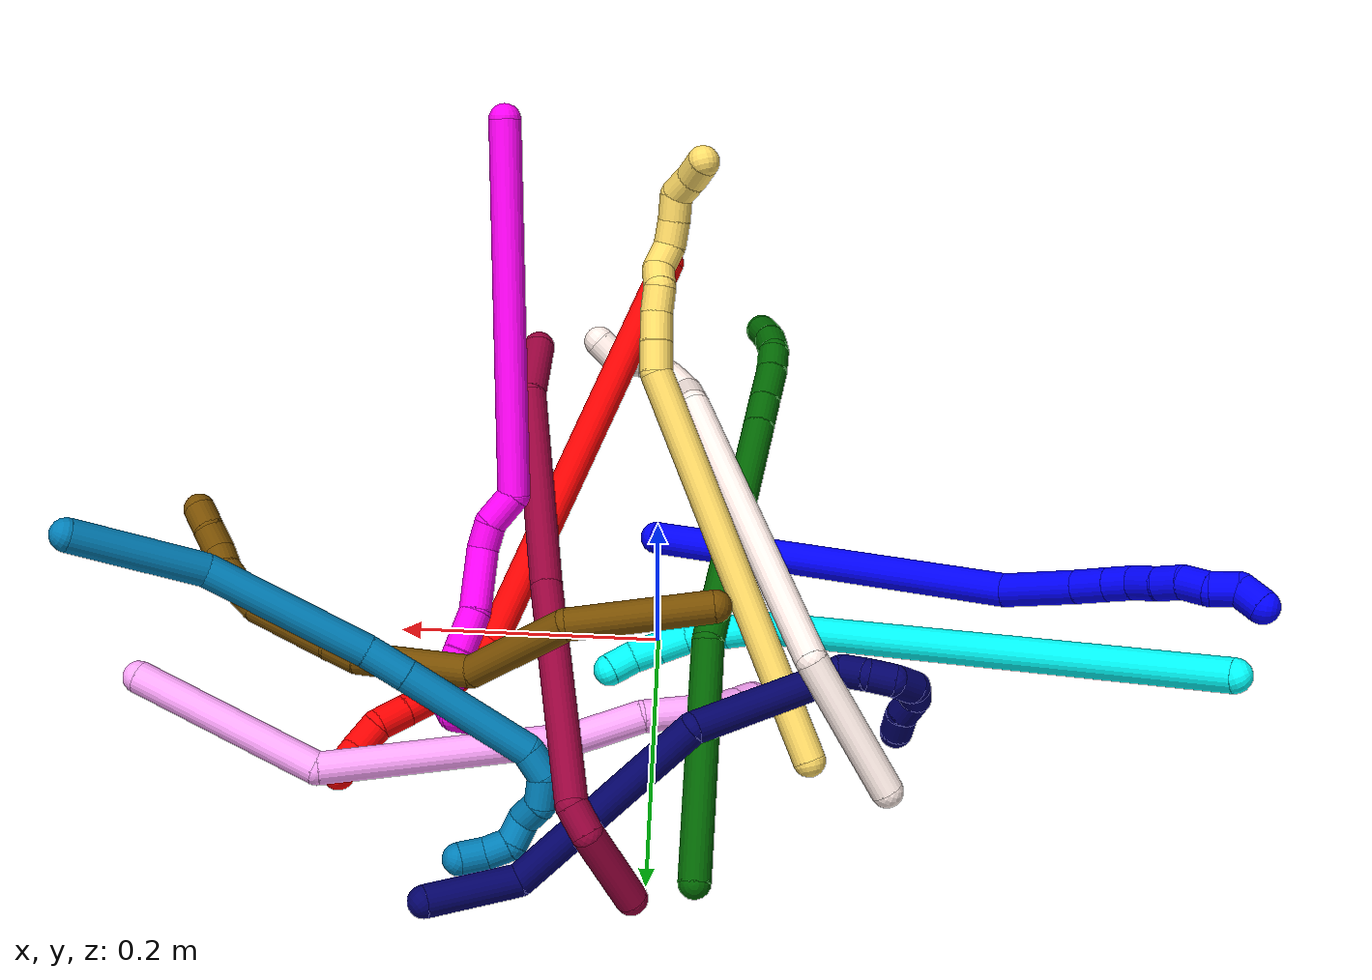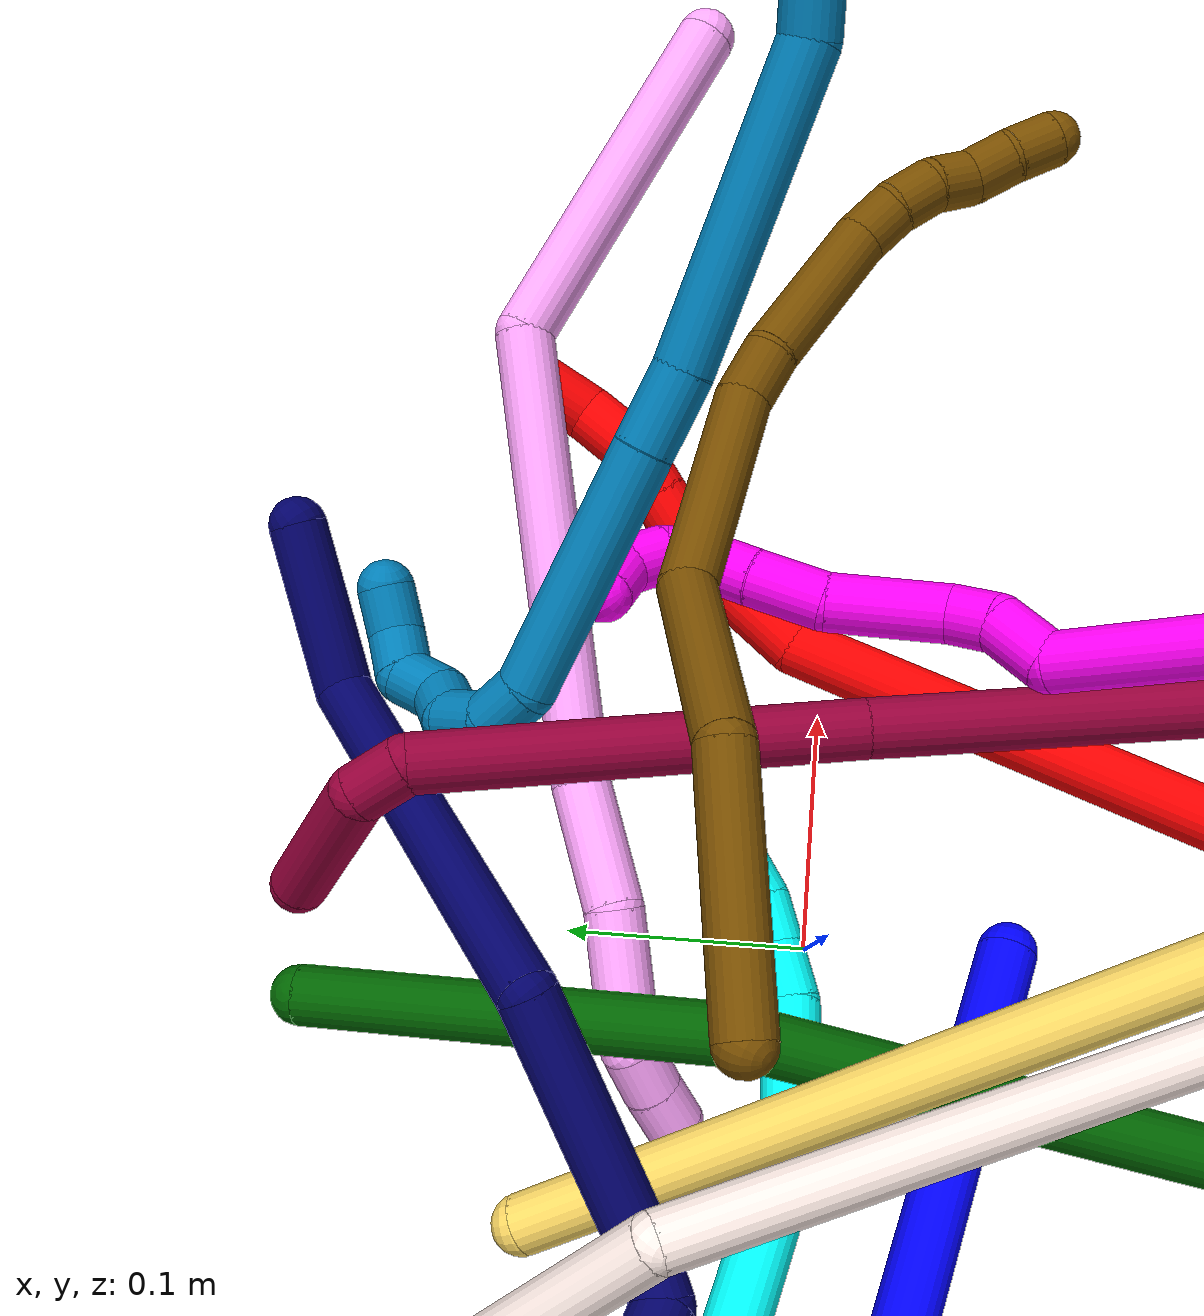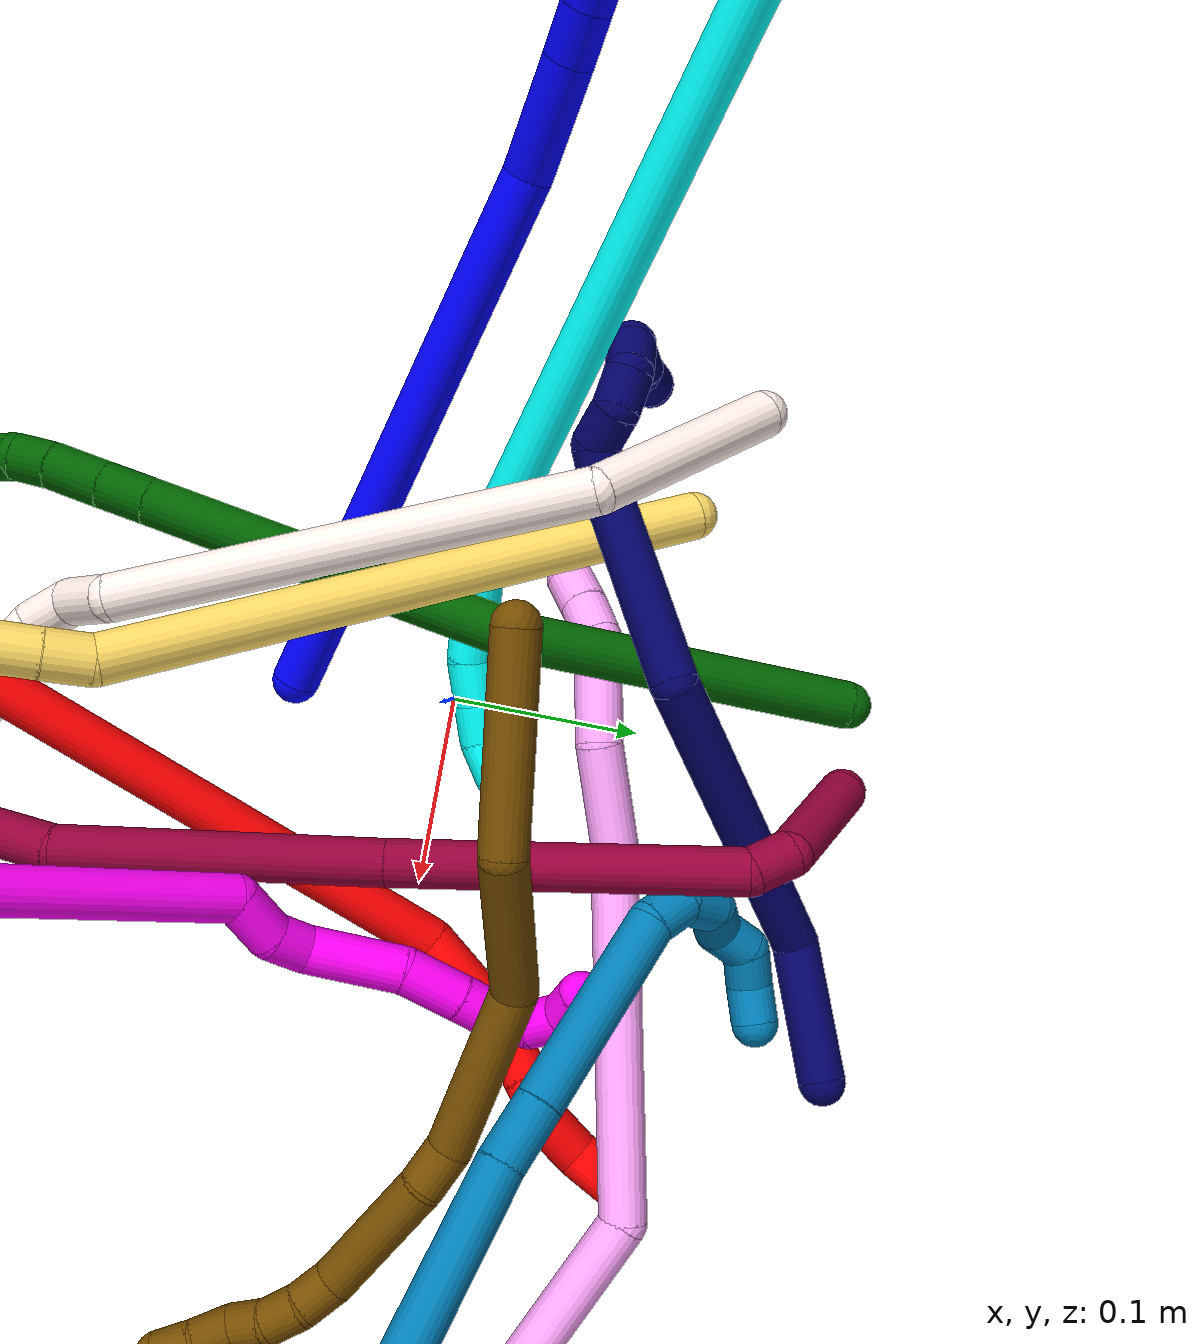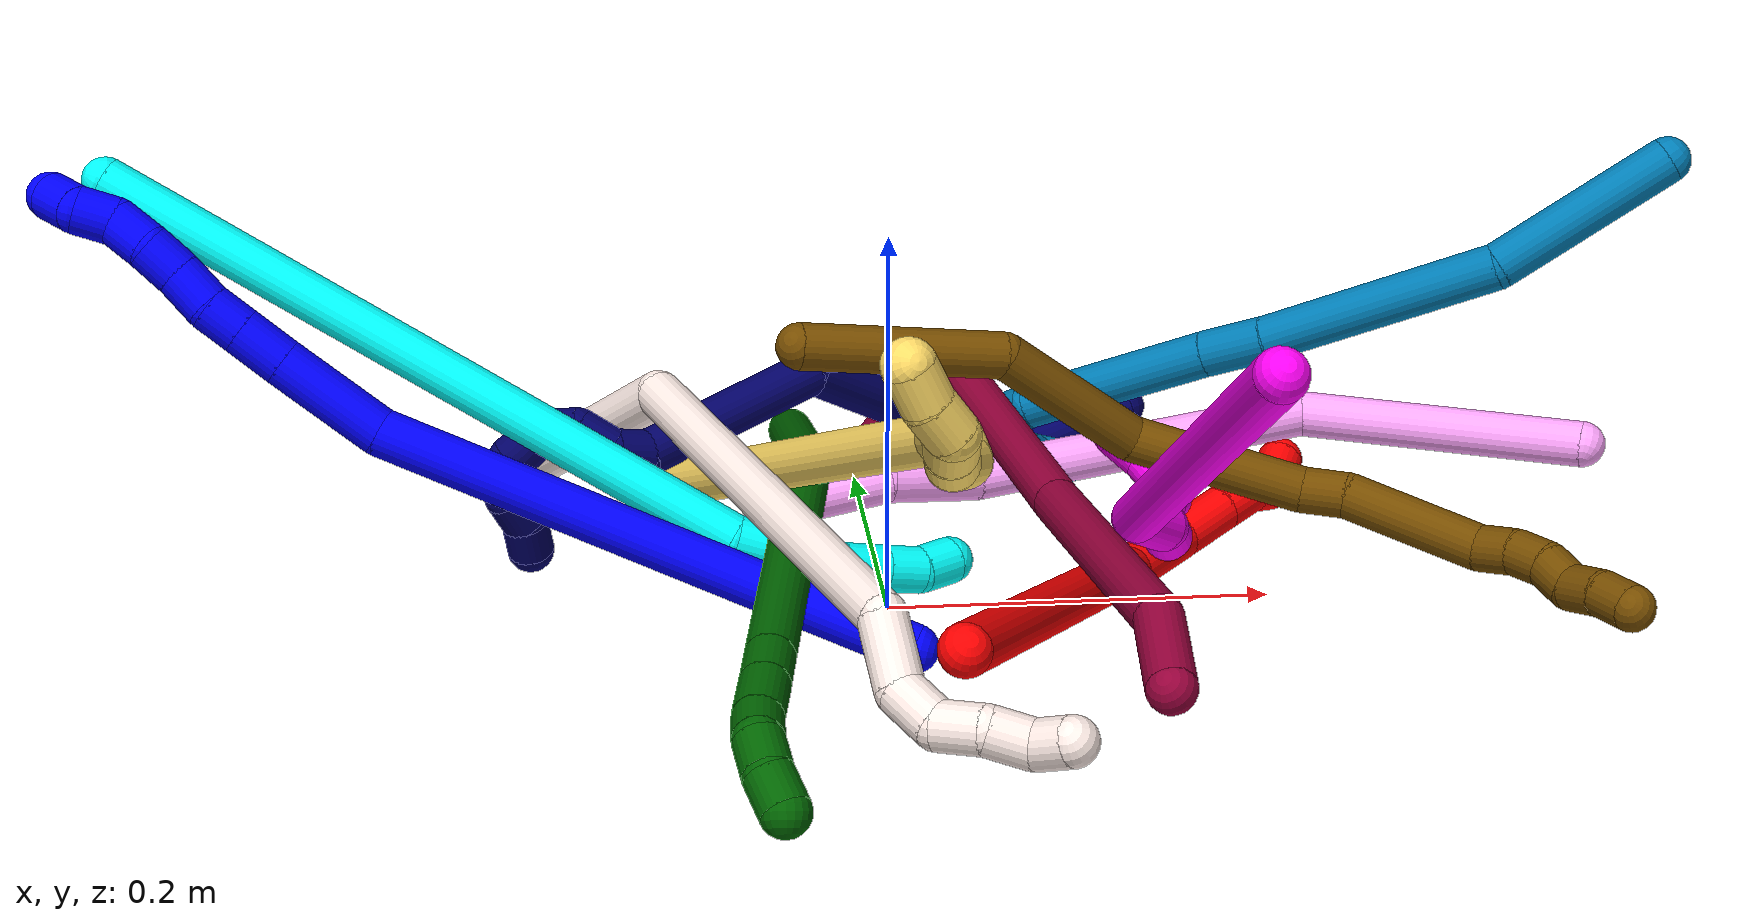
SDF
<sdf version="1.7">
 <world name="default">
  <plugin name="TubeGeneratorPlugin" filename="libtube_generator_plugin.so"/>
  <model name="photoneo_s_sensor">
   <static>1</static>
   <pose>0 0 2 1.57079 1.57079 3.14159</pose>
   <link name="link">
    <inertial><mass>0.1</mass></inertial>
    <sensor name="sensor" type="depth">
     <update_rate>30</update_rate>
     <camera>
      <horizontal_fov>1.22</horizontal_fov>
      <image><width>1920</width><height>1200</height><format>B8G8R8</format></image>
      <clip><near>0.1</near><far>4</far></clip>
      <depth_camera><output>points</output></depth_camera>
     </camera>
     <plugin name="camera_plugin" filename="libgazebo_ros_depth_camera.so">
      <baseline>0.2</baseline>
      <alwaysOn>1</alwaysOn>
      <updateRate>0.0</updateRate>
      <cameraName>camera_ir</cameraName>
      <imageTopicName>/camera/color/image_raw</imageTopicName>
      <cameraInfoTopicName>/camera/color/camera_info</cameraInfoTopicName>
      <depthImageTopicName>/camera/depth/image_raw</depthImageTopicName>
      <depthImageCameraInfoTopicName>/camera/depth/camera_info</depthImageCameraInfoTopicName>
      <pointCloudTopicName>/camera/depth/points</pointCloudTopicName>
      <frameName>fr_optical</frameName>
      <pointCloudCutoff>0.1</pointCloudCutoff>
      <pointCloudCutoffMax>2.0</pointCloudCutoffMax>
      <distortionK1>0</distortionK1>
      <distortionK2>0</distortionK2>
      <distortionK3>0</distortionK3>
      <distortionT1>0</distortionT1>
      <distortionT2>0</distortionT2>
      <CxPrime>0</CxPrime>
      <Cx>0</Cx>
      <Cy>0</Cy>
      <focalLength>0</focalLength>
      <hackBaseline>0</hackBaseline>
     </plugin>
    </sensor>
   </link>
  </model>
  <gravity>0 0 -9.8</gravity>
  <magnetic_field>6e-06 2.3e-05 -4.2e-05</magnetic_field>
  <atmosphere type="adiabatic"/>
  <physics name="default_physics" default="0" type="ode">
   <max_step_size>0.003</max_step_size>
   <real_time_factor>1</real_time_factor>
   <real_time_update_rate>1000</real_time_update_rate>
   <max_contacts>10000</max_contacts>
   <ode>
    <solver>
     <type>quick</type>
     <iters>100</iters>
     <sor>1.3</sor>
     <use_dynamic_moi_rescaling>0</use_dynamic_moi_rescaling>
    </solver>
    <constraints>
     <contact_max_correcting_vel>0</contact_max_correcting_vel>
     <contact_surface_layer>0.001</contact_surface_layer>
     <cfm>0</cfm>
     <erp>0.2</erp>
    </constraints>
   </ode>
  </physics>
  <scene><ambient>0.4 0.4 0.4 1</ambient><background>0.7 0.7 0.7 1</background><shadows>0</shadows></scene>
  <audio><device>default</device></audio>
  <spherical_coordinates>
   <surface_model>EARTH_WGS84</surface_model>
   <latitude_deg>0</latitude_deg>
   <longitude_deg>0</longitude_deg>
   <elevation>0</elevation>
   <heading_deg>0</heading_deg>
  </spherical_coordinates>
  <model name="bin">
   <static>1</static>
   <link name="bottom">
    <collision name="collision-bottom">
     <pose>0 0 -0.01 0 -0 0</pose>
     <geometry><box><size>0.8 0.6 0.02</size></box></geometry>
     <surface>
      <friction><ode><mu>100</mu><mu2>100</mu2></ode></friction>
      <contact><collide_bitmask>65535</collide_bitmask></contact>
     </surface>
    </collision>
   </link>
   <link name="west_wall">
    <collision name="collision-west_wall">
     <pose>-0.41 0 0.1 0 -0 0</pose>
     <geometry><box><size>0.02 0.6 0.2</size></box></geometry>
     <surface>
      <friction><ode><mu>100</mu><mu2>100</mu2></ode></friction>
      <contact><collide_bitmask>65535</collide_bitmask></contact>
     </surface>
    </collision>
   </link>
   <link name="east_wall">
    <collision name="collision-east_wall">
     <pose>0.41 0 0.1 0 -0 0</pose>
     <geometry><box><size>0.02 0.6 0.2</size></box></geometry>
     <surface>
      <friction><ode><mu>100</mu><mu2>100</mu2></ode></friction>
      <contact><collide_bitmask>65535</collide_bitmask></contact>
     </surface>
    </collision>
   </link>
   <link name="south_wall">
    <collision name="collision-south_wall">
     <pose>0 -0.31 0.1 0 -0 0</pose>
     <geometry><box><size>0.8 0.02 0.2</size></box></geometry>
     <surface>
      <friction><ode><mu>100</mu><mu2>100</mu2></ode></friction>
      <contact><collide_bitmask>65535</collide_bitmask></contact>
     </surface>
    </collision>
   </link>
   <link name="north_wall">
    <collision name="collision-north_wall">
     <pose>0 0.31 0.1 0 -0 0</pose>
     <geometry><box><size>0.8 0.02 0.2</size></box></geometry>
     <surface>
      <friction><ode><mu>100</mu><mu2>100</mu2></ode></friction>
      <contact><collide_bitmask>65535</collide_bitmask></contact>
     </surface>
    </collision>
   </link>
  </model>
  <model name="1">
   <static>0</static>
   <link name="1">
    <collision name="collision-cylinder-e_1_1_4">
     <pose>-0.01979 0.004411 0.143485 -0.030733 -0.136992 0.002109</pose>
     <geometry><cylinder><radius>0.0125</radius><length>0.289822</length></cylinder></geometry>
     <surface>
      <friction><ode><mu>1.16</mu><mu2>1.16</mu2><slip1>0</slip1><slip2>0</slip2></ode></friction>
      <contact><ode><kp>1e+06</kp><kd>1</kd><max_vel>0</max_vel><min_depth>0.001</min_depth></ode></contact>
     </surface>
    </collision>
    <visual name="visual-cylinder-e_1_1_4">
     <pose>-0.01979 0.004411 0.143485 -0.030733 -0.136992 0.002109</pose>
     <geometry><cylinder><radius>0.0125</radius><length>0.289822</length></cylinder></geometry>
     <material><ambient>0 0 1 1</ambient></material>
    </visual>
    <collision name="collision-cylinder-e_2_4_5">
     <pose>-0.050587 0.014248 0.314199 -0.196702 -0.377458 0.037688</pose>
     <geometry><cylinder><radius>0.0125</radius><length>0.059733</length></cylinder></geometry>
     <surface>
      <friction><ode><mu>1.16</mu><mu2>1.16</mu2><slip1>0</slip1><slip2>0</slip2></ode></friction>
      <contact><ode><kp>1e+06</kp><kd>1</kd><max_vel>0</max_vel><min_depth>0.001</min_depth></ode></contact>
     </surface>
    </collision>
    <visual name="visual-cylinder-e_2_4_5">
     <pose>-0.050587 0.014248 0.314199 -0.196702 -0.377458 0.037688</pose>
     <geometry><cylinder><radius>0.0125</radius><length>0.059733</length></cylinder></geometry>
     <material><ambient>0 0 1 1</ambient></material>
    </visual>
    <collision name="collision-cylinder-e_3_5_6">
     <pose>-0.066638 0.022307 0.353091 -0.221995 -0.399172 0.045083</pose>
     <geometry><cylinder><radius>0.0125</radius><length>0.025954</length></cylinder></geometry>
     <surface>
      <friction><ode><mu>1.16</mu><mu2>1.16</mu2><slip1>0</slip1><slip2>0</slip2></ode></friction>
      <contact><ode><kp>1e+06</kp><kd>1</kd><max_vel>0</max_vel><min_depth>0.001</min_depth></ode></contact>
     </surface>
    </collision>
    <visual name="visual-cylinder-e_3_5_6">
     <pose>-0.066638 0.022307 0.353091 -0.221995 -0.399172 0.045083</pose>
     <geometry><cylinder><radius>0.0125</radius><length>0.025954</length></cylinder></geometry>
     <material><ambient>0 0 1 1</ambient></material>
    </visual>
    <collision name="collision-cylinder-e_4_6_7">
     <pose>-0.075537 0.026923 0.373805 -0.215737 -0.394323 0.043256</pose>
     <geometry><cylinder><radius>0.0125</radius><length>0.020069</length></cylinder></geometry>
     <surface>
      <friction><ode><mu>1.16</mu><mu2>1.16</mu2><slip1>0</slip1><slip2>0</slip2></ode></friction>
      <contact><ode><kp>1e+06</kp><kd>1</kd><max_vel>0</max_vel><min_depth>0.001</min_depth></ode></contact>
     </surface>
    </collision>
    <visual name="visual-cylinder-e_4_6_7">
     <pose>-0.075537 0.026923 0.373805 -0.215737 -0.394323 0.043256</pose>
     <geometry><cylinder><radius>0.0125</radius><length>0.020069</length></cylinder></geometry>
     <material><ambient>0 0 1 1</ambient></material>
    </visual>
    <collision name="collision-cylinder-e_5_7_8">
     <pose>-0.085465 0.029739 0.392074 -0.090038 -0.580582 0.026914</pose>
     <geometry><cylinder><radius>0.0125</radius><length>0.022143</length></cylinder></geometry>
     <surface>
      <friction><ode><mu>1.16</mu><mu2>1.16</mu2><slip1>0</slip1><slip2>0</slip2></ode></friction>
      <contact><ode><kp>1e+06</kp><kd>1</kd><max_vel>0</max_vel><min_depth>0.001</min_depth></ode></contact>
     </surface>
    </collision>
    <visual name="visual-cylinder-e_5_7_8">
     <pose>-0.085465 0.029739 0.392074 -0.090038 -0.580582 0.026914</pose>
     <geometry><cylinder><radius>0.0125</radius><length>0.022143</length></cylinder></geometry>
     <material><ambient>0 0 1 1</ambient></material>
    </visual>
    <collision name="collision-cylinder-e_6_8_9">
     <pose>-0.096216 0.032348 0.410132 -0.198421 -0.478729 0.048573</pose>
     <geometry><cylinder><radius>0.0125</radius><length>0.020312</length></cylinder></geometry>
     <surface>
      <friction><ode><mu>1.16</mu><mu2>1.16</mu2><slip1>0</slip1><slip2>0</slip2></ode></friction>
      <contact><ode><kp>1e+06</kp><kd>1</kd><max_vel>0</max_vel><min_depth>0.001</min_depth></ode></contact>
     </surface>
    </collision>
    <visual name="visual-cylinder-e_6_8_9">
     <pose>-0.096216 0.032348 0.410132 -0.198421 -0.478729 0.048573</pose>
     <geometry><cylinder><radius>0.0125</radius><length>0.020312</length></cylinder></geometry>
     <material><ambient>0 0 1 1</ambient></material>
    </visual>
    <collision name="collision-cylinder-e_7_9_10">
     <pose>-0.105142 0.033193 0.428839 0.09411 -0.40477 -0.019324</pose>
     <geometry><cylinder><radius>0.0125</radius><length>0.021571</length></cylinder></geometry>
     <surface>
      <friction><ode><mu>1.16</mu><mu2>1.16</mu2><slip1>0</slip1><slip2>0</slip2></ode></friction>
      <contact><ode><kp>1e+06</kp><kd>1</kd><max_vel>0</max_vel><min_depth>0.001</min_depth></ode></contact>
     </surface>
    </collision>
    <visual name="visual-cylinder-e_7_9_10">
     <pose>-0.105142 0.033193 0.428839 0.09411 -0.40477 -0.019324</pose>
     <geometry><cylinder><radius>0.0125</radius><length>0.021571</length></cylinder></geometry>
     <material><ambient>0 0 1 1</ambient></material>
    </visual>
    <collision name="collision-cylinder-e_8_10_11">
     <pose>-0.109767 0.034047 0.448688 -0.177101 -0.037272 0.00331</pose>
     <geometry><cylinder><radius>0.0125</radius><length>0.020287</length></cylinder></geometry>
     <surface>
      <friction><ode><mu>1.16</mu><mu2>1.16</mu2><slip1>0</slip1><slip2>0</slip2></ode></friction>
      <contact><ode><kp>1e+06</kp><kd>1</kd><max_vel>0</max_vel><min_depth>0.001</min_depth></ode></contact>
     </surface>
    </collision>
    <visual name="visual-cylinder-e_8_10_11">
     <pose>-0.109767 0.034047 0.448688 -0.177101 -0.037272 0.00331</pose>
     <geometry><cylinder><radius>0.0125</radius><length>0.020287</length></cylinder></geometry>
     <material><ambient>0 0 1 1</ambient></material>
    </visual>
    <collision name="collision-cylinder-e_9_11_2">
     <pose>-0.11219 0.031226 0.467365 0.48706 -0.204796 -0.051051</pose>
     <geometry><cylinder><radius>0.0125</radius><length>0.020108</length></cylinder></geometry>
     <surface>
      <friction><ode><mu>1.16</mu><mu2>1.16</mu2><slip1>0</slip1><slip2>0</slip2></ode></friction>
      <contact><ode><kp>1e+06</kp><kd>1</kd><max_vel>0</max_vel><min_depth>0.001</min_depth></ode></contact>
     </surface>
    </collision>
    <visual name="visual-cylinder-e_9_11_2">
     <pose>-0.11219 0.031226 0.467365 0.48706 -0.204796 -0.051051</pose>
     <geometry><cylinder><radius>0.0125</radius><length>0.020108</length></cylinder></geometry>
     <material><ambient>0 0 1 1</ambient></material>
    </visual>
    <collision name="collision-sphere-2">
     <pose>-0.114235 0.026619 0.476064 0 -0 0</pose>
     <geometry><sphere><radius>0.0125</radius></sphere></geometry>
     <surface>
      <friction><ode><mu>1.16</mu><mu2>1.16</mu2><slip1>0</slip1><slip2>0</slip2></ode></friction>
      <contact><ode><kp>1e+06</kp><kd>1</kd><max_vel>0</max_vel><min_depth>0.001</min_depth></ode></contact>
     </surface>
    </collision>
    <visual name="visual-sphere-2">
     <pose>-0.114235 0.026619 0.476064 0 -0 0</pose>
     <geometry><sphere><radius>0.0125</radius></sphere></geometry>
     <material><ambient>0 0 1 1</ambient></material>
    </visual>
    <collision name="collision-sphere-11">
     <pose>-0.110145 0.035833 0.458666 0 -0 0</pose>
     <geometry><sphere><radius>0.0125</radius></sphere></geometry>
     <surface>
      <friction><ode><mu>1.16</mu><mu2>1.16</mu2><slip1>0</slip1><slip2>0</slip2></ode></friction>
      <contact><ode><kp>1e+06</kp><kd>1</kd><max_vel>0</max_vel><min_depth>0.001</min_depth></ode></contact>
     </surface>
    </collision>
    <visual name="visual-sphere-11">
     <pose>-0.110145 0.035833 0.458666 0 -0 0</pose>
     <geometry><sphere><radius>0.0125</radius></sphere></geometry>
     <material><ambient>0 0 1 1</ambient></material>
    </visual>
    <collision name="collision-sphere-10">
     <pose>-0.109389 0.032262 0.43871 0 -0 0</pose>
     <geometry><sphere><radius>0.0125</radius></sphere></geometry>
     <surface>
      <friction><ode><mu>1.16</mu><mu2>1.16</mu2><slip1>0</slip1><slip2>0</slip2></ode></friction>
      <contact><ode><kp>1e+06</kp><kd>1</kd><max_vel>0</max_vel><min_depth>0.001</min_depth></ode></contact>
     </surface>
    </collision>
    <visual name="visual-sphere-10">
     <pose>-0.109389 0.032262 0.43871 0 -0 0</pose>
     <geometry><sphere><radius>0.0125</radius></sphere></geometry>
     <material><ambient>0 0 1 1</ambient></material>
    </visual>
    <collision name="collision-sphere-9">
     <pose>-0.100894 0.034125 0.418969 0 -0 0</pose>
     <geometry><sphere><radius>0.0125</radius></sphere></geometry>
     <surface>
      <friction><ode><mu>1.16</mu><mu2>1.16</mu2><slip1>0</slip1><slip2>0</slip2></ode></friction>
      <contact><ode><kp>1e+06</kp><kd>1</kd><max_vel>0</max_vel><min_depth>0.001</min_depth></ode></contact>
     </surface>
    </collision>
    <visual name="visual-sphere-9">
     <pose>-0.100894 0.034125 0.418969 0 -0 0</pose>
     <geometry><sphere><radius>0.0125</radius></sphere></geometry>
     <material><ambient>0 0 1 1</ambient></material>
    </visual>
    <collision name="collision-sphere-4">
     <pose>-0.039579 0.008822 0.286971 0 -0 0</pose>
     <geometry><sphere><radius>0.0125</radius></sphere></geometry>
     <surface>
      <friction><ode><mu>1.16</mu><mu2>1.16</mu2><slip1>0</slip1><slip2>0</slip2></ode></friction>
      <contact><ode><kp>1e+06</kp><kd>1</kd><max_vel>0</max_vel><min_depth>0.001</min_depth></ode></contact>
     </surface>
    </collision>
    <visual name="visual-sphere-4">
     <pose>-0.039579 0.008822 0.286971 0 -0 0</pose>
     <geometry><sphere><radius>0.0125</radius></sphere></geometry>
     <material><ambient>0 0 1 1</ambient></material>
    </visual>
    <collision name="collision-sphere-1">
     <geometry><sphere><radius>0.0125</radius></sphere></geometry>
     <surface>
      <friction><ode><mu>1.16</mu><mu2>1.16</mu2><slip1>0</slip1><slip2>0</slip2></ode></friction>
      <contact><ode><kp>1e+06</kp><kd>1</kd><max_vel>0</max_vel><min_depth>0.001</min_depth></ode></contact>
     </surface>
    </collision>
    <visual name="visual-sphere-1">
     <geometry><sphere><radius>0.0125</radius></sphere></geometry>
     <material><ambient>0 0 1 1</ambient></material>
    </visual>
    <collision name="collision-sphere-8">
     <pose>-0.091538 0.030571 0.401294 0 -0 0</pose>
     <geometry><sphere><radius>0.0125</radius></sphere></geometry>
     <surface>
      <friction><ode><mu>1.16</mu><mu2>1.16</mu2><slip1>0</slip1><slip2>0</slip2></ode></friction>
      <contact><ode><kp>1e+06</kp><kd>1</kd><max_vel>0</max_vel><min_depth>0.001</min_depth></ode></contact>
     </surface>
    </collision>
    <visual name="visual-sphere-8">
     <pose>-0.091538 0.030571 0.401294 0 -0 0</pose>
     <geometry><sphere><radius>0.0125</radius></sphere></geometry>
     <material><ambient>0 0 1 1</ambient></material>
    </visual>
    <collision name="collision-sphere-5">
     <pose>-0.061594 0.019675 0.341428 0 -0 0</pose>
     <geometry><sphere><radius>0.0125</radius></sphere></geometry>
     <surface>
      <friction><ode><mu>1.16</mu><mu2>1.16</mu2><slip1>0</slip1><slip2>0</slip2></ode></friction>
      <contact><ode><kp>1e+06</kp><kd>1</kd><max_vel>0</max_vel><min_depth>0.001</min_depth></ode></contact>
     </surface>
    </collision>
    <visual name="visual-sphere-5">
     <pose>-0.061594 0.019675 0.341428 0 -0 0</pose>
     <geometry><sphere><radius>0.0125</radius></sphere></geometry>
     <material><ambient>0 0 1 1</ambient></material>
    </visual>
    <collision name="collision-sphere-6">
     <pose>-0.071681 0.02494 0.364755 0 -0 0</pose>
     <geometry><sphere><radius>0.0125</radius></sphere></geometry>
     <surface>
      <friction><ode><mu>1.16</mu><mu2>1.16</mu2><slip1>0</slip1><slip2>0</slip2></ode></friction>
      <contact><ode><kp>1e+06</kp><kd>1</kd><max_vel>0</max_vel><min_depth>0.001</min_depth></ode></contact>
     </surface>
    </collision>
    <visual name="visual-sphere-6">
     <pose>-0.071681 0.02494 0.364755 0 -0 0</pose>
     <geometry><sphere><radius>0.0125</radius></sphere></geometry>
     <material><ambient>0 0 1 1</ambient></material>
    </visual>
    <collision name="collision-sphere-7">
     <pose>-0.079392 0.028906 0.382855 0 -0 0</pose>
     <geometry><sphere><radius>0.0125</radius></sphere></geometry>
     <surface>
      <friction><ode><mu>1.16</mu><mu2>1.16</mu2><slip1>0</slip1><slip2>0</slip2></ode></friction>
      <contact><ode><kp>1e+06</kp><kd>1</kd><max_vel>0</max_vel><min_depth>0.001</min_depth></ode></contact>
     </surface>
    </collision>
    <visual name="visual-sphere-7">
     <pose>-0.079392 0.028906 0.382855 0 -0 0</pose>
     <geometry><sphere><radius>0.0125</radius></sphere></geometry>
     <material><ambient>0 0 1 1</ambient></material>
    </visual>
    <inertial>
     <pose>-0.045201 0.013198 0.243566 0 -0 0</pose>
     <mass>0.5</mass>
     <inertia>
      <ixx>0.002047</ixx>
      <ixy>0</ixy>
      <ixz>0</ixz>
      <iyy>0.002078</iyy>
      <iyz>0</iyz>
      <izz>0.000261</izz>
     </inertia>
    </inertial>
   </link>
   <pose>0.005235 -0.083805 0.01149 1.10322 1.12122 -2.26018</pose>
  </model>
  <model name="2">
   <static>0</static>
   <link name="2">
    <collision name="collision-cylinder-e_1_1_4">
     <pose>0.046314 0.094687 -0.130837 -2.51513 0.279273 -0.818844</pose>
     <geometry><cylinder><radius>0.0125</radius><length>0.336029</length></cylinder></geometry>
     <surface>
      <friction><ode><mu>1.16</mu><mu2>1.16</mu2><slip1>0</slip1><slip2>0</slip2></ode></friction>
      <contact><ode><kp>1e+06</kp><kd>1</kd><max_vel>0</max_vel><min_depth>0.001</min_depth></ode></contact>
     </surface>
    </collision>
    <visual name="visual-cylinder-e_1_1_4">
     <pose>0.046314 0.094687 -0.130837 -2.51513 0.279273 -0.818844</pose>
     <geometry><cylinder><radius>0.0125</radius><length>0.336029</length></cylinder></geometry>
     <material><ambient>1 0 0 1</ambient></material>
    </visual>
    <collision name="collision-cylinder-e_2_4_5">
     <pose>0.105173 0.209655 -0.275004 -2.15231 0.477052 -0.847063</pose>
     <geometry><cylinder><radius>0.0125</radius><length>0.054641</length></cylinder></geometry>
     <surface>
      <friction><ode><mu>1.16</mu><mu2>1.16</mu2><slip1>0</slip1><slip2>0</slip2></ode></friction>
      <contact><ode><kp>1e+06</kp><kd>1</kd><max_vel>0</max_vel><min_depth>0.001</min_depth></ode></contact>
     </surface>
    </collision>
    <visual name="visual-cylinder-e_2_4_5">
     <pose>0.105173 0.209655 -0.275004 -2.15231 0.477052 -0.847063</pose>
     <geometry><cylinder><radius>0.0125</radius><length>0.054641</length></cylinder></geometry>
     <material><ambient>1 0 0 1</ambient></material>
    </visual>
    <collision name="collision-cylinder-e_3_5_6">
     <pose>0.127466 0.24372 -0.291862 -1.82128 0.600727 -0.759219</pose>
     <geometry><cylinder><radius>0.0125</radius><length>0.034495</length></cylinder></geometry>
     <surface>
      <friction><ode><mu>1.16</mu><mu2>1.16</mu2><slip1>0</slip1><slip2>0</slip2></ode></friction>
      <contact><ode><kp>1e+06</kp><kd>1</kd><max_vel>0</max_vel><min_depth>0.001</min_depth></ode></contact>
     </surface>
    </collision>
    <visual name="visual-cylinder-e_3_5_6">
     <pose>0.127466 0.24372 -0.291862 -1.82128 0.600727 -0.759219</pose>
     <geometry><cylinder><radius>0.0125</radius><length>0.034495</length></cylinder></geometry>
     <material><ambient>1 0 0 1</ambient></material>
    </visual>
    <collision name="collision-cylinder-e_4_6_7">
     <pose>0.144227 0.26717 -0.297821 -1.81729 0.61304 -0.771325</pose>
     <geometry><cylinder><radius>0.0125</radius><length>0.024375</length></cylinder></geometry>
     <surface>
      <friction><ode><mu>1.16</mu><mu2>1.16</mu2><slip1>0</slip1><slip2>0</slip2></ode></friction>
      <contact><ode><kp>1e+06</kp><kd>1</kd><max_vel>0</max_vel><min_depth>0.001</min_depth></ode></contact>
     </surface>
    </collision>
    <visual name="visual-cylinder-e_4_6_7">
     <pose>0.144227 0.26717 -0.297821 -1.81729 0.61304 -0.771325</pose>
     <geometry><cylinder><radius>0.0125</radius><length>0.024375</length></cylinder></geometry>
     <material><ambient>1 0 0 1</ambient></material>
    </visual>
    <collision name="collision-cylinder-e_5_7_8">
     <pose>0.157746 0.283796 -0.308313 -2.42933 0.548477 -1.295</pose>
     <geometry><cylinder><radius>0.0125</radius><length>0.024958</length></cylinder></geometry>
     <surface>
      <friction><ode><mu>1.16</mu><mu2>1.16</mu2><slip1>0</slip1><slip2>0</slip2></ode></friction>
      <contact><ode><kp>1e+06</kp><kd>1</kd><max_vel>0</max_vel><min_depth>0.001</min_depth></ode></contact>
     </surface>
    </collision>
    <visual name="visual-cylinder-e_5_7_8">
     <pose>0.157746 0.283796 -0.308313 -2.42933 0.548477 -1.295</pose>
     <geometry><cylinder><radius>0.0125</radius><length>0.024958</length></cylinder></geometry>
     <material><ambient>1 0 0 1</ambient></material>
    </visual>
    <collision name="collision-cylinder-e_6_8_2">
     <pose>0.166068 0.30247 -0.321071 -1.95225 0.142925 -0.210895</pose>
     <geometry><cylinder><radius>0.0125</radius><length>0.025503</length></cylinder></geometry>
     <surface>
      <friction><ode><mu>1.16</mu><mu2>1.16</mu2><slip1>0</slip1><slip2>0</slip2></ode></friction>
      <contact><ode><kp>1e+06</kp><kd>1</kd><max_vel>0</max_vel><min_depth>0.001</min_depth></ode></contact>
     </surface>
    </collision>
    <visual name="visual-cylinder-e_6_8_2">
     <pose>0.166068 0.30247 -0.321071 -1.95225 0.142925 -0.210895</pose>
     <geometry><cylinder><radius>0.0125</radius><length>0.025503</length></cylinder></geometry>
     <material><ambient>1 0 0 1</ambient></material>
    </visual>
    <collision name="collision-sphere-2">
     <pose>0.167885 0.314185 -0.32577 0 -0 0</pose>
     <geometry><sphere><radius>0.0125</radius></sphere></geometry>
     <surface>
      <friction><ode><mu>1.16</mu><mu2>1.16</mu2><slip1>0</slip1><slip2>0</slip2></ode></friction>
      <contact><ode><kp>1e+06</kp><kd>1</kd><max_vel>0</max_vel><min_depth>0.001</min_depth></ode></contact>
     </surface>
    </collision>
    <visual name="visual-sphere-2">
     <pose>0.167885 0.314185 -0.32577 0 -0 0</pose>
     <geometry><sphere><radius>0.0125</radius></sphere></geometry>
     <material><ambient>1 0 0 1</ambient></material>
    </visual>
    <collision name="collision-sphere-4">
     <pose>0.092629 0.189374 -0.261673 0 -0 0</pose>
     <geometry><sphere><radius>0.0125</radius></sphere></geometry>
     <surface>
      <friction><ode><mu>1.16</mu><mu2>1.16</mu2><slip1>0</slip1><slip2>0</slip2></ode></friction>
      <contact><ode><kp>1e+06</kp><kd>1</kd><max_vel>0</max_vel><min_depth>0.001</min_depth></ode></contact>
     </surface>
    </collision>
    <visual name="visual-sphere-4">
     <pose>0.092629 0.189374 -0.261673 0 -0 0</pose>
     <geometry><sphere><radius>0.0125</radius></sphere></geometry>
     <material><ambient>1 0 0 1</ambient></material>
    </visual>
    <collision name="collision-sphere-1">
     <geometry><sphere><radius>0.0125</radius></sphere></geometry>
     <surface>
      <friction><ode><mu>1.16</mu><mu2>1.16</mu2><slip1>0</slip1><slip2>0</slip2></ode></friction>
      <contact><ode><kp>1e+06</kp><kd>1</kd><max_vel>0</max_vel><min_depth>0.001</min_depth></ode></contact>
     </surface>
    </collision>
    <visual name="visual-sphere-1">
     <geometry><sphere><radius>0.0125</radius></sphere></geometry>
     <material><ambient>1 0 0 1</ambient></material>
    </visual>
    <collision name="collision-sphere-8">
     <pose>0.164252 0.290756 -0.316373 0 -0 0</pose>
     <geometry><sphere><radius>0.0125</radius></sphere></geometry>
     <surface>
      <friction><ode><mu>1.16</mu><mu2>1.16</mu2><slip1>0</slip1><slip2>0</slip2></ode></friction>
      <contact><ode><kp>1e+06</kp><kd>1</kd><max_vel>0</max_vel><min_depth>0.001</min_depth></ode></contact>
     </surface>
    </collision>
    <visual name="visual-sphere-8">
     <pose>0.164252 0.290756 -0.316373 0 -0 0</pose>
     <geometry><sphere><radius>0.0125</radius></sphere></geometry>
     <material><ambient>1 0 0 1</ambient></material>
    </visual>
    <collision name="collision-sphere-5">
     <pose>0.117718 0.229936 -0.288336 0 -0 0</pose>
     <geometry><sphere><radius>0.0125</radius></sphere></geometry>
     <surface>
      <friction><ode><mu>1.16</mu><mu2>1.16</mu2><slip1>0</slip1><slip2>0</slip2></ode></friction>
      <contact><ode><kp>1e+06</kp><kd>1</kd><max_vel>0</max_vel><min_depth>0.001</min_depth></ode></contact>
     </surface>
    </collision>
    <visual name="visual-sphere-5">
     <pose>0.117718 0.229936 -0.288336 0 -0 0</pose>
     <geometry><sphere><radius>0.0125</radius></sphere></geometry>
     <material><ambient>1 0 0 1</ambient></material>
    </visual>
    <collision name="collision-sphere-6">
     <pose>0.137215 0.257504 -0.295389 0 -0 0</pose>
     <geometry><sphere><radius>0.0125</radius></sphere></geometry>
     <surface>
      <friction><ode><mu>1.16</mu><mu2>1.16</mu2><slip1>0</slip1><slip2>0</slip2></ode></friction>
      <contact><ode><kp>1e+06</kp><kd>1</kd><max_vel>0</max_vel><min_depth>0.001</min_depth></ode></contact>
     </surface>
    </collision>
    <visual name="visual-sphere-6">
     <pose>0.137215 0.257504 -0.295389 0 -0 0</pose>
     <geometry><sphere><radius>0.0125</radius></sphere></geometry>
     <material><ambient>1 0 0 1</ambient></material>
    </visual>
    <collision name="collision-sphere-7">
     <pose>0.15124 0.276837 -0.300253 0 -0 0</pose>
     <geometry><sphere><radius>0.0125</radius></sphere></geometry>
     <surface>
      <friction><ode><mu>1.16</mu><mu2>1.16</mu2><slip1>0</slip1><slip2>0</slip2></ode></friction>
      <contact><ode><kp>1e+06</kp><kd>1</kd><max_vel>0</max_vel><min_depth>0.001</min_depth></ode></contact>
     </surface>
    </collision>
    <visual name="visual-sphere-7">
     <pose>0.15124 0.276837 -0.300253 0 -0 0</pose>
     <geometry><sphere><radius>0.0125</radius></sphere></geometry>
     <material><ambient>1 0 0 1</ambient></material>
    </visual>
    <inertial>
     <pose>0.074789 0.145979 -0.184403 0 -0 0</pose>
     <mass>0.5</mass>
     <inertia>
      <ixx>-0.000132</ixx>
      <ixy>0</ixy>
      <ixz>0</ixz>
      <iyy>-0.003604</iyy>
      <iyz>0</iyz>
      <izz>-0.002723</izz>
     </inertia>
    </inertial>
   </link>
   <pose>0.00555 -0.28803 0.095546 0.758011 0.293228 -0.167032</pose>
  </model>
  <model name="3">
   <static>0</static>
   <link name="3">
    <collision name="collision-cylinder-e_1_1_4">
     <pose>0.082164 -0.035865 -0.164601 2.92705 0.453782 2.26873</pose>
     <geometry><cylinder><radius>0.0125</radius><length>0.374864</length></cylinder></geometry>
     <surface>
      <friction><ode><mu>1.16</mu><mu2>1.16</mu2><slip1>0</slip1><slip2>0</slip2></ode></friction>
      <contact><ode><kp>1e+06</kp><kd>1</kd><max_vel>0</max_vel><min_depth>0.001</min_depth></ode></contact>
     </surface>
    </collision>
    <visual name="visual-cylinder-e_1_1_4">
     <pose>0.082164 -0.035865 -0.164601 2.92705 0.453782 2.26873</pose>
     <geometry><cylinder><radius>0.0125</radius><length>0.374864</length></cylinder></geometry>
     <material><ambient>0.003922 1 0.996078 1</ambient></material>
    </visual>
    <collision name="collision-cylinder-e_2_4_5">
     <pose>0.167229 -0.071087 -0.342678 -3.09386 0.211795 -2.69977</pose>
     <geometry><cylinder><radius>0.0125</radius><length>0.0276</length></cylinder></geometry>
     <surface>
      <friction><ode><mu>1.16</mu><mu2>1.16</mu2><slip1>0</slip1><slip2>0</slip2></ode></friction>
      <contact><ode><kp>1e+06</kp><kd>1</kd><max_vel>0</max_vel><min_depth>0.001</min_depth></ode></contact>
     </surface>
    </collision>
    <visual name="visual-cylinder-e_2_4_5">
     <pose>0.167229 -0.071087 -0.342678 -3.09386 0.211795 -2.69977</pose>
     <geometry><cylinder><radius>0.0125</radius><length>0.0276</length></cylinder></geometry>
     <material><ambient>0.003922 1 0.996078 1</ambient></material>
    </visual>
    <collision name="collision-cylinder-e_3_5_6">
     <pose>0.173451 -0.069166 -0.37144 -3.05824 0.213216 -2.39842</pose>
     <geometry><cylinder><radius>0.0125</radius><length>0.03139</length></cylinder></geometry>
     <surface>
      <friction><ode><mu>1.16</mu><mu2>1.16</mu2><slip1>0</slip1><slip2>0</slip2></ode></friction>
      <contact><ode><kp>1e+06</kp><kd>1</kd><max_vel>0</max_vel><min_depth>0.001</min_depth></ode></contact>
     </surface>
    </collision>
    <visual name="visual-cylinder-e_3_5_6">
     <pose>0.173451 -0.069166 -0.37144 -3.05824 0.213216 -2.39842</pose>
     <geometry><cylinder><radius>0.0125</radius><length>0.03139</length></cylinder></geometry>
     <material><ambient>0.003922 1 0.996078 1</ambient></material>
    </visual>
    <collision name="collision-cylinder-e_4_6_7">
     <pose>0.176426 -0.06525 -0.398292 -2.91726 -0.02917 0.257555</pose>
     <geometry><cylinder><radius>0.0125</radius><length>0.023736</length></cylinder></geometry>
     <surface>
      <friction><ode><mu>1.16</mu><mu2>1.16</mu2><slip1>0</slip1><slip2>0</slip2></ode></friction>
      <contact><ode><kp>1e+06</kp><kd>1</kd><max_vel>0</max_vel><min_depth>0.001</min_depth></ode></contact>
     </surface>
    </collision>
    <visual name="visual-cylinder-e_4_6_7">
     <pose>0.176426 -0.06525 -0.398292 -2.91726 -0.02917 0.257555</pose>
     <geometry><cylinder><radius>0.0125</radius><length>0.023736</length></cylinder></geometry>
     <material><ambient>0.003922 1 0.996078 1</ambient></material>
    </visual>
    <collision name="collision-cylinder-e_5_7_8">
     <pose>0.17577 -0.060061 -0.42027 -2.90138 -0.028948 0.238738</pose>
     <geometry><cylinder><radius>0.0125</radius><length>0.021448</length></cylinder></geometry>
     <surface>
      <friction><ode><mu>1.16</mu><mu2>1.16</mu2><slip1>0</slip1><slip2>0</slip2></ode></friction>
      <contact><ode><kp>1e+06</kp><kd>1</kd><max_vel>0</max_vel><min_depth>0.001</min_depth></ode></contact>
     </surface>
    </collision>
    <visual name="visual-cylinder-e_5_7_8">
     <pose>0.17577 -0.060061 -0.42027 -2.90138 -0.028948 0.238738</pose>
     <geometry><cylinder><radius>0.0125</radius><length>0.021448</length></cylinder></geometry>
     <material><ambient>0.003922 1 0.996078 1</ambient></material>
    </visual>
    <collision name="collision-cylinder-e_6_8_2">
     <pose>0.172913 -0.052532 -0.439546 -2.62993 -0.24543 0.881219</pose>
     <geometry><cylinder><radius>0.0125</radius><length>0.020963</length></cylinder></geometry>
     <surface>
      <friction><ode><mu>1.16</mu><mu2>1.16</mu2><slip1>0</slip1><slip2>0</slip2></ode></friction>
      <contact><ode><kp>1e+06</kp><kd>1</kd><max_vel>0</max_vel><min_depth>0.001</min_depth></ode></contact>
     </surface>
    </collision>
    <visual name="visual-cylinder-e_6_8_2">
     <pose>0.172913 -0.052532 -0.439546 -2.62993 -0.24543 0.881219</pose>
     <geometry><cylinder><radius>0.0125</radius><length>0.020963</length></cylinder></geometry>
     <material><ambient>0.003922 1 0.996078 1</ambient></material>
    </visual>
    <collision name="collision-sphere-2">
     <pose>0.170366 -0.047554 -0.448412 0 -0 0</pose>
     <geometry><sphere><radius>0.0125</radius></sphere></geometry>
     <surface>
      <friction><ode><mu>1.16</mu><mu2>1.16</mu2><slip1>0</slip1><slip2>0</slip2></ode></friction>
      <contact><ode><kp>1e+06</kp><kd>1</kd><max_vel>0</max_vel><min_depth>0.001</min_depth></ode></contact>
     </surface>
    </collision>
    <visual name="visual-sphere-2">
     <pose>0.170366 -0.047554 -0.448412 0 -0 0</pose>
     <geometry><sphere><radius>0.0125</radius></sphere></geometry>
     <material><ambient>0.003922 1 0.996078 1</ambient></material>
    </visual>
    <collision name="collision-sphere-4">
     <pose>0.164329 -0.071731 -0.329202 0 -0 0</pose>
     <geometry><sphere><radius>0.0125</radius></sphere></geometry>
     <surface>
      <friction><ode><mu>1.16</mu><mu2>1.16</mu2><slip1>0</slip1><slip2>0</slip2></ode></friction>
      <contact><ode><kp>1e+06</kp><kd>1</kd><max_vel>0</max_vel><min_depth>0.001</min_depth></ode></contact>
     </surface>
    </collision>
    <visual name="visual-sphere-4">
     <pose>0.164329 -0.071731 -0.329202 0 -0 0</pose>
     <geometry><sphere><radius>0.0125</radius></sphere></geometry>
     <material><ambient>0.003922 1 0.996078 1</ambient></material>
    </visual>
    <collision name="collision-sphere-1">
     <geometry><sphere><radius>0.0125</radius></sphere></geometry>
     <surface>
      <friction><ode><mu>1.16</mu><mu2>1.16</mu2><slip1>0</slip1><slip2>0</slip2></ode></friction>
      <contact><ode><kp>1e+06</kp><kd>1</kd><max_vel>0</max_vel><min_depth>0.001</min_depth></ode></contact>
     </surface>
    </collision>
    <visual name="visual-sphere-1">
     <geometry><sphere><radius>0.0125</radius></sphere></geometry>
     <material><ambient>0.003922 1 0.996078 1</ambient></material>
    </visual>
    <collision name="collision-sphere-8">
     <pose>0.17546 -0.05751 -0.430681 0 -0 0</pose>
     <geometry><sphere><radius>0.0125</radius></sphere></geometry>
     <surface>
      <friction><ode><mu>1.16</mu><mu2>1.16</mu2><slip1>0</slip1><slip2>0</slip2></ode></friction>
      <contact><ode><kp>1e+06</kp><kd>1</kd><max_vel>0</max_vel><min_depth>0.001</min_depth></ode></contact>
     </surface>
    </collision>
    <visual name="visual-sphere-8">
     <pose>0.17546 -0.05751 -0.430681 0 -0 0</pose>
     <geometry><sphere><radius>0.0125</radius></sphere></geometry>
     <material><ambient>0.003922 1 0.996078 1</ambient></material>
    </visual>
    <collision name="collision-sphere-5">
     <pose>0.17013 -0.070443 -0.356154 0 -0 0</pose>
     <geometry><sphere><radius>0.0125</radius></sphere></geometry>
     <surface>
      <friction><ode><mu>1.16</mu><mu2>1.16</mu2><slip1>0</slip1><slip2>0</slip2></ode></friction>
      <contact><ode><kp>1e+06</kp><kd>1</kd><max_vel>0</max_vel><min_depth>0.001</min_depth></ode></contact>
     </surface>
    </collision>
    <visual name="visual-sphere-5">
     <pose>0.17013 -0.070443 -0.356154 0 -0 0</pose>
     <geometry><sphere><radius>0.0125</radius></sphere></geometry>
     <material><ambient>0.003922 1 0.996078 1</ambient></material>
    </visual>
    <collision name="collision-sphere-6">
     <pose>0.176773 -0.067889 -0.386727 0 -0 0</pose>
     <geometry><sphere><radius>0.0125</radius></sphere></geometry>
     <surface>
      <friction><ode><mu>1.16</mu><mu2>1.16</mu2><slip1>0</slip1><slip2>0</slip2></ode></friction>
      <contact><ode><kp>1e+06</kp><kd>1</kd><max_vel>0</max_vel><min_depth>0.001</min_depth></ode></contact>
     </surface>
    </collision>
    <visual name="visual-sphere-6">
     <pose>0.176773 -0.067889 -0.386727 0 -0 0</pose>
     <geometry><sphere><radius>0.0125</radius></sphere></geometry>
     <material><ambient>0.003922 1 0.996078 1</ambient></material>
    </visual>
    <collision name="collision-sphere-7">
     <pose>0.17608 -0.062611 -0.409858 0 -0 0</pose>
     <geometry><sphere><radius>0.0125</radius></sphere></geometry>
     <surface>
      <friction><ode><mu>1.16</mu><mu2>1.16</mu2><slip1>0</slip1><slip2>0</slip2></ode></friction>
      <contact><ode><kp>1e+06</kp><kd>1</kd><max_vel>0</max_vel><min_depth>0.001</min_depth></ode></contact>
     </surface>
    </collision>
    <visual name="visual-sphere-7">
     <pose>0.17608 -0.062611 -0.409858 0 -0 0</pose>
     <geometry><sphere><radius>0.0125</radius></sphere></geometry>
     <material><ambient>0.003922 1 0.996078 1</ambient></material>
    </visual>
    <inertial>
     <pose>0.104886 -0.043032 -0.221004 0 -0 0</pose>
     <mass>0.5</mass>
     <inertia>
      <ixx>0.0005</ixx>
      <ixy>0</ixy>
      <ixz>0</ixz>
      <iyy>0.006109</iyy>
      <iyz>0</iyz>
      <izz>-0.001126</izz>
     </inertia>
    </inertial>
   </link>
   <pose>-0.397509 0.1016 0.212309 1.13137 -0.180629 -1.23198</pose>
  </model>
  <model name="4">
   <static>0</static>
   <link name="4">
    <collision name="collision-cylinder-e_1_1_4">
     <pose>-0.07615 0.01696 0.007076 -1.17552 -1.33399 0.966332</pose>
     <geometry><cylinder><radius>0.0125</radius><length>0.156672</length></cylinder></geometry>
     <surface>
      <friction><ode><mu>1.16</mu><mu2>1.16</mu2><slip1>0</slip1><slip2>0</slip2></ode></friction>
      <contact><ode><kp>1e+06</kp><kd>1</kd><max_vel>0</max_vel><min_depth>0.001</min_depth></ode></contact>
     </surface>
    </collision>
    <visual name="visual-cylinder-e_1_1_4">
     <pose>-0.07615 0.01696 0.007076 -1.17552 -1.33399 0.966332</pose>
     <geometry><cylinder><radius>0.0125</radius><length>0.156672</length></cylinder></geometry>
     <material><ambient>1 0.65098 0.996078 1</ambient></material>
    </visual>
    <collision name="collision-cylinder-e_2_4_5">
     <pose>-0.237279 0.024224 -0.02999 2.92536 -1.082 -2.78412</pose>
     <geometry><cylinder><radius>0.0125</radius><length>0.1925</length></cylinder></geometry>
     <surface>
      <friction><ode><mu>1.16</mu><mu2>1.16</mu2><slip1>0</slip1><slip2>0</slip2></ode></friction>
      <contact><ode><kp>1e+06</kp><kd>1</kd><max_vel>0</max_vel><min_depth>0.001</min_depth></ode></contact>
     </surface>
    </collision>
    <visual name="visual-cylinder-e_2_4_5">
     <pose>-0.237279 0.024224 -0.02999 2.92536 -1.082 -2.78412</pose>
     <geometry><cylinder><radius>0.0125</radius><length>0.1925</length></cylinder></geometry>
     <material><ambient>1 0.65098 0.996078 1</ambient></material>
    </visual>
    <collision name="collision-cylinder-e_3_5_6">
     <pose>-0.344829 0.005333 -0.085193 2.44805 -1.00346 -1.97656</pose>
     <geometry><cylinder><radius>0.0125</radius><length>0.053527</length></cylinder></geometry>
     <surface>
      <friction><ode><mu>1.16</mu><mu2>1.16</mu2><slip1>0</slip1><slip2>0</slip2></ode></friction>
      <contact><ode><kp>1e+06</kp><kd>1</kd><max_vel>0</max_vel><min_depth>0.001</min_depth></ode></contact>
     </surface>
    </collision>
    <visual name="visual-cylinder-e_3_5_6">
     <pose>-0.344829 0.005333 -0.085193 2.44805 -1.00346 -1.97656</pose>
     <geometry><cylinder><radius>0.0125</radius><length>0.053527</length></cylinder></geometry>
     <material><ambient>1 0.65098 0.996078 1</ambient></material>
    </visual>
    <collision name="collision-cylinder-e_4_6_7">
     <pose>-0.391847 -0.005667 -0.10947 3.00586 -1.0713 -2.91355</pose>
     <geometry><cylinder><radius>0.0125</radius><length>0.055702</length></cylinder></geometry>
     <surface>
      <friction><ode><mu>1.16</mu><mu2>1.16</mu2><slip1>0</slip1><slip2>0</slip2></ode></friction>
      <contact><ode><kp>1e+06</kp><kd>1</kd><max_vel>0</max_vel><min_depth>0.001</min_depth></ode></contact>
     </surface>
    </collision>
    <visual name="visual-cylinder-e_4_6_7">
     <pose>-0.391847 -0.005667 -0.10947 3.00586 -1.0713 -2.91355</pose>
     <geometry><cylinder><radius>0.0125</radius><length>0.055702</length></cylinder></geometry>
     <material><ambient>1 0.65098 0.996078 1</ambient></material>
    </visual>
    <collision name="collision-cylinder-e_5_7_8">
     <pose>-0.421782 -0.006266 -0.131853 -3.01074 -0.535633 2.67285</pose>
     <geometry><cylinder><radius>0.0125</radius><length>0.021501</length></cylinder></geometry>
     <surface>
      <friction><ode><mu>1.16</mu><mu2>1.16</mu2><slip1>0</slip1><slip2>0</slip2></ode></friction>
      <contact><ode><kp>1e+06</kp><kd>1</kd><max_vel>0</max_vel><min_depth>0.001</min_depth></ode></contact>
     </surface>
    </collision>
    <visual name="visual-cylinder-e_5_7_8">
     <pose>-0.421782 -0.006266 -0.131853 -3.01074 -0.535633 2.67285</pose>
     <geometry><cylinder><radius>0.0125</radius><length>0.021501</length></cylinder></geometry>
     <material><ambient>1 0.65098 0.996078 1</ambient></material>
    </visual>
    <collision name="collision-cylinder-e_6_8_2">
     <pose>-0.431823 -0.004136 -0.149929 -3.0383 -0.470263 2.71657</pose>
     <geometry><cylinder><radius>0.0125</radius><length>0.020098</length></cylinder></geometry>
     <surface>
      <friction><ode><mu>1.16</mu><mu2>1.16</mu2><slip1>0</slip1><slip2>0</slip2></ode></friction>
      <contact><ode><kp>1e+06</kp><kd>1</kd><max_vel>0</max_vel><min_depth>0.001</min_depth></ode></contact>
     </surface>
    </collision>
    <visual name="visual-cylinder-e_6_8_2">
     <pose>-0.431823 -0.004136 -0.149929 -3.0383 -0.470263 2.71657</pose>
     <geometry><cylinder><radius>0.0125</radius><length>0.020098</length></cylinder></geometry>
     <material><ambient>1 0.65098 0.996078 1</ambient></material>
    </visual>
    <collision name="collision-sphere-2">
     <pose>-0.436376 -0.003212 -0.15884 0 -0 0</pose>
     <geometry><sphere><radius>0.0125</radius></sphere></geometry>
     <surface>
      <friction><ode><mu>1.16</mu><mu2>1.16</mu2><slip1>0</slip1><slip2>0</slip2></ode></friction>
      <contact><ode><kp>1e+06</kp><kd>1</kd><max_vel>0</max_vel><min_depth>0.001</min_depth></ode></contact>
     </surface>
    </collision>
    <visual name="visual-sphere-2">
     <pose>-0.436376 -0.003212 -0.15884 0 -0 0</pose>
     <geometry><sphere><radius>0.0125</radius></sphere></geometry>
     <material><ambient>1 0.65098 0.996078 1</ambient></material>
    </visual>
    <collision name="collision-sphere-4">
     <pose>-0.1523 0.033921 0.014153 0 -0 0</pose>
     <geometry><sphere><radius>0.0125</radius></sphere></geometry>
     <surface>
      <friction><ode><mu>1.16</mu><mu2>1.16</mu2><slip1>0</slip1><slip2>0</slip2></ode></friction>
      <contact><ode><kp>1e+06</kp><kd>1</kd><max_vel>0</max_vel><min_depth>0.001</min_depth></ode></contact>
     </surface>
    </collision>
    <visual name="visual-sphere-4">
     <pose>-0.1523 0.033921 0.014153 0 -0 0</pose>
     <geometry><sphere><radius>0.0125</radius></sphere></geometry>
     <material><ambient>1 0.65098 0.996078 1</ambient></material>
    </visual>
    <collision name="collision-sphere-1">
     <geometry><sphere><radius>0.0125</radius></sphere></geometry>
     <surface>
      <friction><ode><mu>1.16</mu><mu2>1.16</mu2><slip1>0</slip1><slip2>0</slip2></ode></friction>
      <contact><ode><kp>1e+06</kp><kd>1</kd><max_vel>0</max_vel><min_depth>0.001</min_depth></ode></contact>
     </surface>
    </collision>
    <visual name="visual-sphere-1">
     <geometry><sphere><radius>0.0125</radius></sphere></geometry>
     <material><ambient>1 0.65098 0.996078 1</ambient></material>
    </visual>
    <collision name="collision-sphere-8">
     <pose>-0.427269 -0.005059 -0.141019 0 -0 0</pose>
     <geometry><sphere><radius>0.0125</radius></sphere></geometry>
     <surface>
      <friction><ode><mu>1.16</mu><mu2>1.16</mu2><slip1>0</slip1><slip2>0</slip2></ode></friction>
      <contact><ode><kp>1e+06</kp><kd>1</kd><max_vel>0</max_vel><min_depth>0.001</min_depth></ode></contact>
     </surface>
    </collision>
    <visual name="visual-sphere-8">
     <pose>-0.427269 -0.005059 -0.141019 0 -0 0</pose>
     <geometry><sphere><radius>0.0125</radius></sphere></geometry>
     <material><ambient>1 0.65098 0.996078 1</ambient></material>
    </visual>
    <collision name="collision-sphere-5">
     <pose>-0.322258 0.014527 -0.074133 0 -0 0</pose>
     <geometry><sphere><radius>0.0125</radius></sphere></geometry>
     <surface>
      <friction><ode><mu>1.16</mu><mu2>1.16</mu2><slip1>0</slip1><slip2>0</slip2></ode></friction>
      <contact><ode><kp>1e+06</kp><kd>1</kd><max_vel>0</max_vel><min_depth>0.001</min_depth></ode></contact>
     </surface>
    </collision>
    <visual name="visual-sphere-5">
     <pose>-0.322258 0.014527 -0.074133 0 -0 0</pose>
     <geometry><sphere><radius>0.0125</radius></sphere></geometry>
     <material><ambient>1 0.65098 0.996078 1</ambient></material>
    </visual>
    <collision name="collision-sphere-6">
     <pose>-0.367399 -0.003862 -0.096253 0 -0 0</pose>
     <geometry><sphere><radius>0.0125</radius></sphere></geometry>
     <surface>
      <friction><ode><mu>1.16</mu><mu2>1.16</mu2><slip1>0</slip1><slip2>0</slip2></ode></friction>
      <contact><ode><kp>1e+06</kp><kd>1</kd><max_vel>0</max_vel><min_depth>0.001</min_depth></ode></contact>
     </surface>
    </collision>
    <visual name="visual-sphere-6">
     <pose>-0.367399 -0.003862 -0.096253 0 -0 0</pose>
     <geometry><sphere><radius>0.0125</radius></sphere></geometry>
     <material><ambient>1 0.65098 0.996078 1</ambient></material>
    </visual>
    <collision name="collision-sphere-7">
     <pose>-0.416296 -0.007472 -0.122688 0 -0 0</pose>
     <geometry><sphere><radius>0.0125</radius></sphere></geometry>
     <surface>
      <friction><ode><mu>1.16</mu><mu2>1.16</mu2><slip1>0</slip1><slip2>0</slip2></ode></friction>
      <contact><ode><kp>1e+06</kp><kd>1</kd><max_vel>0</max_vel><min_depth>0.001</min_depth></ode></contact>
     </surface>
    </collision>
    <visual name="visual-sphere-7">
     <pose>-0.416296 -0.007472 -0.122688 0 -0 0</pose>
     <geometry><sphere><radius>0.0125</radius></sphere></geometry>
     <material><ambient>1 0.65098 0.996078 1</ambient></material>
    </visual>
    <inertial>
     <pose>-0.231277 0.014144 -0.042341 0 -0 0</pose>
     <mass>0.5</mass>
     <inertia>
      <ixx>-0.000313</ixx>
      <ixy>0</ixy>
      <ixz>0</ixz>
      <iyy>0.00089</iyy>
      <iyz>0</iyz>
      <izz>0.000861</izz>
     </inertia>
    </inertial>
   </link>
   <pose>0.387161 0.071746 0.052678 -0.921984 0.118481 -0.233867</pose>
  </model>
  <model name="5">
   <static>0</static>
   <link name="5">
    <collision name="collision-cylinder-e_1_1_4">
     <pose>0.023404 -0.002144 0.155188 0.013815 0.149667 0.001036</pose>
     <geometry><cylinder><radius>0.0125</radius><length>0.313915</length></cylinder></geometry>
     <surface>
      <friction><ode><mu>1.16</mu><mu2>1.16</mu2><slip1>0</slip1><slip2>0</slip2></ode></friction>
      <contact><ode><kp>1e+06</kp><kd>1</kd><max_vel>0</max_vel><min_depth>0.001</min_depth></ode></contact>
     </surface>
    </collision>
    <visual name="visual-cylinder-e_1_1_4">
     <pose>0.023404 -0.002144 0.155188 0.013815 0.149667 0.001036</pose>
     <geometry><cylinder><radius>0.0125</radius><length>0.313915</length></cylinder></geometry>
     <material><ambient>1 0.858824 0.4 1</ambient></material>
    </visual>
    <collision name="collision-cylinder-e_2_4_5">
     <pose>0.044251 -0.005403 0.321786 0.097442 -0.219377 -0.01074</pose>
     <geometry><cylinder><radius>0.0125</radius><length>0.023491</length></cylinder></geometry>
     <surface>
      <friction><ode><mu>1.16</mu><mu2>1.16</mu2><slip1>0</slip1><slip2>0</slip2></ode></friction>
      <contact><ode><kp>1e+06</kp><kd>1</kd><max_vel>0</max_vel><min_depth>0.001</min_depth></ode></contact>
     </surface>
    </collision>
    <visual name="visual-cylinder-e_2_4_5">
     <pose>0.044251 -0.005403 0.321786 0.097442 -0.219377 -0.01074</pose>
     <geometry><cylinder><radius>0.0125</radius><length>0.023491</length></cylinder></geometry>
     <material><ambient>1 0.858824 0.4 1</ambient></material>
    </visual>
    <collision name="collision-cylinder-e_3_5_6">
     <pose>0.039161 -0.008139 0.344027 0.148506 -0.227374 -0.016987</pose>
     <geometry><cylinder><radius>0.0125</radius><length>0.022485</length></cylinder></geometry>
     <surface>
      <friction><ode><mu>1.16</mu><mu2>1.16</mu2><slip1>0</slip1><slip2>0</slip2></ode></friction>
      <contact><ode><kp>1e+06</kp><kd>1</kd><max_vel>0</max_vel><min_depth>0.001</min_depth></ode></contact>
     </surface>
    </collision>
    <visual name="visual-cylinder-e_3_5_6">
     <pose>0.039161 -0.008139 0.344027 0.148506 -0.227374 -0.016987</pose>
     <geometry><cylinder><radius>0.0125</radius><length>0.022485</length></cylinder></geometry>
     <material><ambient>1 0.858824 0.4 1</ambient></material>
    </visual>
    <collision name="collision-cylinder-e_4_6_7">
     <pose>0.033163 -0.010058 0.364285 0.031599 -0.352017 -0.00562</pose>
     <geometry><cylinder><radius>0.0125</radius><length>0.020091</length></cylinder></geometry>
     <surface>
      <friction><ode><mu>1.16</mu><mu2>1.16</mu2><slip1>0</slip1><slip2>0</slip2></ode></friction>
      <contact><ode><kp>1e+06</kp><kd>1</kd><max_vel>0</max_vel><min_depth>0.001</min_depth></ode></contact>
     </surface>
    </collision>
    <visual name="visual-cylinder-e_4_6_7">
     <pose>0.033163 -0.010058 0.364285 0.031599 -0.352017 -0.00562</pose>
     <geometry><cylinder><radius>0.0125</radius><length>0.020091</length></cylinder></geometry>
     <material><ambient>1 0.858824 0.4 1</ambient></material>
    </visual>
    <collision name="collision-cylinder-e_5_7_8">
     <pose>0.028727 -0.016496 0.381547 0.664584 -0.097412 -0.033639</pose>
     <geometry><cylinder><radius>0.0125</radius><length>0.020008</length></cylinder></geometry>
     <surface>
      <friction><ode><mu>1.16</mu><mu2>1.16</mu2><slip1>0</slip1><slip2>0</slip2></ode></friction>
      <contact><ode><kp>1e+06</kp><kd>1</kd><max_vel>0</max_vel><min_depth>0.001</min_depth></ode></contact>
     </surface>
    </collision>
    <visual name="visual-cylinder-e_5_7_8">
     <pose>0.028727 -0.016496 0.381547 0.664584 -0.097412 -0.033639</pose>
     <geometry><cylinder><radius>0.0125</radius><length>0.020008</length></cylinder></geometry>
     <material><ambient>1 0.858824 0.4 1</ambient></material>
    </visual>
    <collision name="collision-cylinder-e_6_8_9">
     <pose>0.021577 -0.023939 0.397146 0.166231 -0.665478 -0.057564</pose>
     <geometry><cylinder><radius>0.0125</radius><length>0.020009</length></cylinder></geometry>
     <surface>
      <friction><ode><mu>1.16</mu><mu2>1.16</mu2><slip1>0</slip1><slip2>0</slip2></ode></friction>
      <contact><ode><kp>1e+06</kp><kd>1</kd><max_vel>0</max_vel><min_depth>0.001</min_depth></ode></contact>
     </surface>
    </collision>
    <visual name="visual-cylinder-e_6_8_9">
     <pose>0.021577 -0.023939 0.397146 0.166231 -0.665478 -0.057564</pose>
     <geometry><cylinder><radius>0.0125</radius><length>0.020009</length></cylinder></geometry>
     <material><ambient>1 0.858824 0.4 1</ambient></material>
    </visual>
    <collision name="collision-cylinder-e_7_9_10">
     <pose>0.011522 -0.023572 0.413973 -0.182021 -0.398177 0.036822</pose>
     <geometry><cylinder><radius>0.0125</radius><length>0.020001</length></cylinder></geometry>
     <surface>
      <friction><ode><mu>1.16</mu><mu2>1.16</mu2><slip1>0</slip1><slip2>0</slip2></ode></friction>
      <contact><ode><kp>1e+06</kp><kd>1</kd><max_vel>0</max_vel><min_depth>0.001</min_depth></ode></contact>
     </surface>
    </collision>
    <visual name="visual-cylinder-e_7_9_10">
     <pose>0.011522 -0.023572 0.413973 -0.182021 -0.398177 0.036822</pose>
     <geometry><cylinder><radius>0.0125</radius><length>0.020001</length></cylinder></geometry>
     <material><ambient>1 0.858824 0.4 1</ambient></material>
    </visual>
    <collision name="collision-cylinder-e_8_10_11">
     <pose>0.004565 -0.019164 0.43215 -0.292146 -0.313056 0.046429</pose>
     <geometry><cylinder><radius>0.0125</radius><length>0.02</length></cylinder></geometry>
     <surface>
      <friction><ode><mu>1.16</mu><mu2>1.16</mu2><slip1>0</slip1><slip2>0</slip2></ode></friction>
      <contact><ode><kp>1e+06</kp><kd>1</kd><max_vel>0</max_vel><min_depth>0.001</min_depth></ode></contact>
     </surface>
    </collision>
    <visual name="visual-cylinder-e_8_10_11">
     <pose>0.004565 -0.019164 0.43215 -0.292146 -0.313056 0.046429</pose>
     <geometry><cylinder><radius>0.0125</radius><length>0.02</length></cylinder></geometry>
     <material><ambient>1 0.858824 0.4 1</ambient></material>
    </visual>
    <collision name="collision-cylinder-e_9_11_12">
     <pose>-0.005456 -0.010217 0.444907 -1.03964 -0.767189 0.454002</pose>
     <geometry><cylinder><radius>0.0125</radius><length>0.02</length></cylinder></geometry>
     <surface>
      <friction><ode><mu>1.16</mu><mu2>1.16</mu2><slip1>0</slip1><slip2>0</slip2></ode></friction>
      <contact><ode><kp>1e+06</kp><kd>1</kd><max_vel>0</max_vel><min_depth>0.001</min_depth></ode></contact>
     </surface>
    </collision>
    <visual name="visual-cylinder-e_9_11_12">
     <pose>-0.005456 -0.010217 0.444907 -1.03964 -0.767189 0.454002</pose>
     <geometry><cylinder><radius>0.0125</radius><length>0.02</length></cylinder></geometry>
     <material><ambient>1 0.858824 0.4 1</ambient></material>
    </visual>
    <collision name="collision-cylinder-e_10_12_2">
     <pose>-0.017849 0.003503 0.452274 -1.11096 -0.57658 0.364046</pose>
     <geometry><cylinder><radius>0.0125</radius><length>0.02</length></cylinder></geometry>
     <surface>
      <friction><ode><mu>1.16</mu><mu2>1.16</mu2><slip1>0</slip1><slip2>0</slip2></ode></friction>
      <contact><ode><kp>1e+06</kp><kd>1</kd><max_vel>0</max_vel><min_depth>0.001</min_depth></ode></contact>
     </surface>
    </collision>
    <visual name="visual-cylinder-e_10_12_2">
     <pose>-0.017849 0.003503 0.452274 -1.11096 -0.57658 0.364046</pose>
     <geometry><cylinder><radius>0.0125</radius><length>0.02</length></cylinder></geometry>
     <material><ambient>1 0.858824 0.4 1</ambient></material>
    </visual>
    <collision name="collision-sphere-2">
     <pose>-0.023301 0.011016 0.455995 0 -0 0</pose>
     <geometry><sphere><radius>0.0125</radius></sphere></geometry>
     <surface>
      <friction><ode><mu>1.16</mu><mu2>1.16</mu2><slip1>0</slip1><slip2>0</slip2></ode></friction>
      <contact><ode><kp>1e+06</kp><kd>1</kd><max_vel>0</max_vel><min_depth>0.001</min_depth></ode></contact>
     </surface>
    </collision>
    <visual name="visual-sphere-2">
     <pose>-0.023301 0.011016 0.455995 0 -0 0</pose>
     <geometry><sphere><radius>0.0125</radius></sphere></geometry>
     <material><ambient>1 0.858824 0.4 1</ambient></material>
    </visual>
    <collision name="collision-sphere-12">
     <pose>-0.012397 -0.00401 0.448553 0 -0 0</pose>
     <geometry><sphere><radius>0.0125</radius></sphere></geometry>
     <surface>
      <friction><ode><mu>1.16</mu><mu2>1.16</mu2><slip1>0</slip1><slip2>0</slip2></ode></friction>
      <contact><ode><kp>1e+06</kp><kd>1</kd><max_vel>0</max_vel><min_depth>0.001</min_depth></ode></contact>
     </surface>
    </collision>
    <visual name="visual-sphere-12">
     <pose>-0.012397 -0.00401 0.448553 0 -0 0</pose>
     <geometry><sphere><radius>0.0125</radius></sphere></geometry>
     <material><ambient>1 0.858824 0.4 1</ambient></material>
    </visual>
    <collision name="collision-sphere-11">
     <pose>0.001485 -0.016423 0.441261 0 -0 0</pose>
     <geometry><sphere><radius>0.0125</radius></sphere></geometry>
     <surface>
      <friction><ode><mu>1.16</mu><mu2>1.16</mu2><slip1>0</slip1><slip2>0</slip2></ode></friction>
      <contact><ode><kp>1e+06</kp><kd>1</kd><max_vel>0</max_vel><min_depth>0.001</min_depth></ode></contact>
     </surface>
    </collision>
    <visual name="visual-sphere-11">
     <pose>0.001485 -0.016423 0.441261 0 -0 0</pose>
     <geometry><sphere><radius>0.0125</radius></sphere></geometry>
     <material><ambient>1 0.858824 0.4 1</ambient></material>
    </visual>
    <collision name="collision-sphere-10">
     <pose>0.007644 -0.021904 0.423039 0 -0 0</pose>
     <geometry><sphere><radius>0.0125</radius></sphere></geometry>
     <surface>
      <friction><ode><mu>1.16</mu><mu2>1.16</mu2><slip1>0</slip1><slip2>0</slip2></ode></friction>
      <contact><ode><kp>1e+06</kp><kd>1</kd><max_vel>0</max_vel><min_depth>0.001</min_depth></ode></contact>
     </surface>
    </collision>
    <visual name="visual-sphere-10">
     <pose>0.007644 -0.021904 0.423039 0 -0 0</pose>
     <geometry><sphere><radius>0.0125</radius></sphere></geometry>
     <material><ambient>1 0.858824 0.4 1</ambient></material>
    </visual>
    <collision name="collision-sphere-9">
     <pose>0.0154 -0.025241 0.404907 0 -0 0</pose>
     <geometry><sphere><radius>0.0125</radius></sphere></geometry>
     <surface>
      <friction><ode><mu>1.16</mu><mu2>1.16</mu2><slip1>0</slip1><slip2>0</slip2></ode></friction>
      <contact><ode><kp>1e+06</kp><kd>1</kd><max_vel>0</max_vel><min_depth>0.001</min_depth></ode></contact>
     </surface>
    </collision>
    <visual name="visual-sphere-9">
     <pose>0.0154 -0.025241 0.404907 0 -0 0</pose>
     <geometry><sphere><radius>0.0125</radius></sphere></geometry>
     <material><ambient>1 0.858824 0.4 1</ambient></material>
    </visual>
    <collision name="collision-sphere-4">
     <pose>0.046807 -0.004288 0.310376 0 -0 0</pose>
     <geometry><sphere><radius>0.0125</radius></sphere></geometry>
     <surface>
      <friction><ode><mu>1.16</mu><mu2>1.16</mu2><slip1>0</slip1><slip2>0</slip2></ode></friction>
      <contact><ode><kp>1e+06</kp><kd>1</kd><max_vel>0</max_vel><min_depth>0.001</min_depth></ode></contact>
     </surface>
    </collision>
    <visual name="visual-sphere-4">
     <pose>0.046807 -0.004288 0.310376 0 -0 0</pose>
     <geometry><sphere><radius>0.0125</radius></sphere></geometry>
     <material><ambient>1 0.858824 0.4 1</ambient></material>
    </visual>
    <collision name="collision-sphere-1">
     <geometry><sphere><radius>0.0125</radius></sphere></geometry>
     <surface>
      <friction><ode><mu>1.16</mu><mu2>1.16</mu2><slip1>0</slip1><slip2>0</slip2></ode></friction>
      <contact><ode><kp>1e+06</kp><kd>1</kd><max_vel>0</max_vel><min_depth>0.001</min_depth></ode></contact>
     </surface>
    </collision>
    <visual name="visual-sphere-1">
     <geometry><sphere><radius>0.0125</radius></sphere></geometry>
     <material><ambient>1 0.858824 0.4 1</ambient></material>
    </visual>
    <collision name="collision-sphere-8">
     <pose>0.027754 -0.022637 0.389385 0 -0 0</pose>
     <geometry><sphere><radius>0.0125</radius></sphere></geometry>
     <surface>
      <friction><ode><mu>1.16</mu><mu2>1.16</mu2><slip1>0</slip1><slip2>0</slip2></ode></friction>
      <contact><ode><kp>1e+06</kp><kd>1</kd><max_vel>0</max_vel><min_depth>0.001</min_depth></ode></contact>
     </surface>
    </collision>
    <visual name="visual-sphere-8">
     <pose>0.027754 -0.022637 0.389385 0 -0 0</pose>
     <geometry><sphere><radius>0.0125</radius></sphere></geometry>
     <material><ambient>1 0.858824 0.4 1</ambient></material>
    </visual>
    <collision name="collision-sphere-5">
     <pose>0.041695 -0.006519 0.333195 0 -0 0</pose>
     <geometry><sphere><radius>0.0125</radius></sphere></geometry>
     <surface>
      <friction><ode><mu>1.16</mu><mu2>1.16</mu2><slip1>0</slip1><slip2>0</slip2></ode></friction>
      <contact><ode><kp>1e+06</kp><kd>1</kd><max_vel>0</max_vel><min_depth>0.001</min_depth></ode></contact>
     </surface>
    </collision>
    <visual name="visual-sphere-5">
     <pose>0.041695 -0.006519 0.333195 0 -0 0</pose>
     <geometry><sphere><radius>0.0125</radius></sphere></geometry>
     <material><ambient>1 0.858824 0.4 1</ambient></material>
    </visual>
    <collision name="collision-sphere-6">
     <pose>0.036627 -0.00976 0.35486 0 -0 0</pose>
     <geometry><sphere><radius>0.0125</radius></sphere></geometry>
     <surface>
      <friction><ode><mu>1.16</mu><mu2>1.16</mu2><slip1>0</slip1><slip2>0</slip2></ode></friction>
      <contact><ode><kp>1e+06</kp><kd>1</kd><max_vel>0</max_vel><min_depth>0.001</min_depth></ode></contact>
     </surface>
    </collision>
    <visual name="visual-sphere-6">
     <pose>0.036627 -0.00976 0.35486 0 -0 0</pose>
     <geometry><sphere><radius>0.0125</radius></sphere></geometry>
     <material><ambient>1 0.858824 0.4 1</ambient></material>
    </visual>
    <collision name="collision-sphere-7">
     <pose>0.0297 -0.010356 0.37371 0 -0 0</pose>
     <geometry><sphere><radius>0.0125</radius></sphere></geometry>
     <surface>
      <friction><ode><mu>1.16</mu><mu2>1.16</mu2><slip1>0</slip1><slip2>0</slip2></ode></friction>
      <contact><ode><kp>1e+06</kp><kd>1</kd><max_vel>0</max_vel><min_depth>0.001</min_depth></ode></contact>
     </surface>
    </collision>
    <visual name="visual-sphere-7">
     <pose>0.0297 -0.010356 0.37371 0 -0 0</pose>
     <geometry><sphere><radius>0.0125</radius></sphere></geometry>
     <material><ambient>1 0.858824 0.4 1</ambient></material>
    </visual>
    <inertial>
     <pose>0.02159 -0.005966 0.243553 0 -0 0</pose>
     <mass>0.5</mass>
     <inertia>
      <ixx>0.002575</ixx>
      <ixy>0</ixy>
      <ixz>0</ixz>
      <iyy>0.002607</iyy>
      <iyz>0</iyz>
      <izz>-0.000311</izz>
     </inertia>
    </inertial>
   </link>
   <pose>-0.118313 0.107067 0.03204 1.15443 0.120013 0.239807</pose>
  </model>
  <model name="6">
   <static>0</static>
   <link name="6">
    <collision name="collision-cylinder-e_1_1_4">
     <pose>0.000366 -0.087559 -0.021463 1.81118 0.004055 0.005168</pose>
     <geometry><cylinder><radius>0.0125</radius><length>0.180304</length></cylinder></geometry>
     <surface>
      <friction><ode><mu>1.16</mu><mu2>1.16</mu2><slip1>0</slip1><slip2>0</slip2></ode></friction>
      <contact><ode><kp>1e+06</kp><kd>1</kd><max_vel>0</max_vel><min_depth>0.001</min_depth></ode></contact>
     </surface>
    </collision>
    <visual name="visual-cylinder-e_1_1_4">
     <pose>0.000366 -0.087559 -0.021463 1.81118 0.004055 0.005168</pose>
     <geometry><cylinder><radius>0.0125</radius><length>0.180304</length></cylinder></geometry>
     <material><ambient>0 0.392157 0.003922 1</ambient></material>
    </visual>
    <collision name="collision-cylinder-e_2_4_5">
     <pose>-0.013832 -0.258174 -0.099459 2.16843 -0.143944 -0.270904</pose>
     <geometry><cylinder><radius>0.0125</radius><length>0.20304</length></cylinder></geometry>
     <surface>
      <friction><ode><mu>1.16</mu><mu2>1.16</mu2><slip1>0</slip1><slip2>0</slip2></ode></friction>
      <contact><ode><kp>1e+06</kp><kd>1</kd><max_vel>0</max_vel><min_depth>0.001</min_depth></ode></contact>
     </surface>
    </collision>
    <visual name="visual-cylinder-e_2_4_5">
     <pose>-0.013832 -0.258174 -0.099459 2.16843 -0.143944 -0.270904</pose>
     <geometry><cylinder><radius>0.0125</radius><length>0.20304</length></cylinder></geometry>
     <material><ambient>0 0.392157 0.003922 1</ambient></material>
    </visual>
    <collision name="collision-cylinder-e_3_5_6">
     <pose>-0.030198 -0.351897 -0.163282 2.17031 -0.138681 -0.261672</pose>
     <geometry><cylinder><radius>0.0125</radius><length>0.026091</length></cylinder></geometry>
     <surface>
      <friction><ode><mu>1.16</mu><mu2>1.16</mu2><slip1>0</slip1><slip2>0</slip2></ode></friction>
      <contact><ode><kp>1e+06</kp><kd>1</kd><max_vel>0</max_vel><min_depth>0.001</min_depth></ode></contact>
     </surface>
    </collision>
    <visual name="visual-cylinder-e_3_5_6">
     <pose>-0.030198 -0.351897 -0.163282 2.17031 -0.138681 -0.261672</pose>
     <geometry><cylinder><radius>0.0125</radius><length>0.026091</length></cylinder></geometry>
     <material><ambient>0 0.392157 0.003922 1</ambient></material>
    </visual>
    <collision name="collision-cylinder-e_4_6_7">
     <pose>-0.034244 -0.374867 -0.179028 2.17293 -0.149142 -0.28211</pose>
     <geometry><cylinder><radius>0.0125</radius><length>0.030194</length></cylinder></geometry>
     <surface>
      <friction><ode><mu>1.16</mu><mu2>1.16</mu2><slip1>0</slip1><slip2>0</slip2></ode></friction>
      <contact><ode><kp>1e+06</kp><kd>1</kd><max_vel>0</max_vel><min_depth>0.001</min_depth></ode></contact>
     </surface>
    </collision>
    <visual name="visual-cylinder-e_4_6_7">
     <pose>-0.034244 -0.374867 -0.179028 2.17293 -0.149142 -0.28211</pose>
     <geometry><cylinder><radius>0.0125</radius><length>0.030194</length></cylinder></geometry>
     <material><ambient>0 0.392157 0.003922 1</ambient></material>
    </visual>
    <collision name="collision-cylinder-e_5_7_8">
     <pose>-0.03684 -0.395615 -0.192869 2.13847 -0.035187 -0.064156</pose>
     <geometry><cylinder><radius>0.0125</radius><length>0.020043</length></cylinder></geometry>
     <surface>
      <friction><ode><mu>1.16</mu><mu2>1.16</mu2><slip1>0</slip1><slip2>0</slip2></ode></friction>
      <contact><ode><kp>1e+06</kp><kd>1</kd><max_vel>0</max_vel><min_depth>0.001</min_depth></ode></contact>
     </surface>
    </collision>
    <visual name="visual-cylinder-e_5_7_8">
     <pose>-0.03684 -0.395615 -0.192869 2.13847 -0.035187 -0.064156</pose>
     <geometry><cylinder><radius>0.0125</radius><length>0.020043</length></cylinder></geometry>
     <material><ambient>0 0.392157 0.003922 1</ambient></material>
    </visual>
    <collision name="collision-cylinder-e_6_8_9">
     <pose>-0.035409 -0.409781 -0.206298 2.52329 0.178765 0.547128</pose>
     <geometry><cylinder><radius>0.0125</radius><length>0.020062</length></cylinder></geometry>
     <surface>
      <friction><ode><mu>1.16</mu><mu2>1.16</mu2><slip1>0</slip1><slip2>0</slip2></ode></friction>
      <contact><ode><kp>1e+06</kp><kd>1</kd><max_vel>0</max_vel><min_depth>0.001</min_depth></ode></contact>
     </surface>
    </collision>
    <visual name="visual-cylinder-e_6_8_9">
     <pose>-0.035409 -0.409781 -0.206298 2.52329 0.178765 0.547128</pose>
     <geometry><cylinder><radius>0.0125</radius><length>0.020062</length></cylinder></geometry>
     <material><ambient>0 0.392157 0.003922 1</ambient></material>
    </visual>
    <collision name="collision-cylinder-e_7_9_2">
     <pose>-0.030156 -0.419463 -0.222999 2.71265 0.349451 1.36213</pose>
     <geometry><cylinder><radius>0.0125</radius><length>0.020267</length></cylinder></geometry>
     <surface>
      <friction><ode><mu>1.16</mu><mu2>1.16</mu2><slip1>0</slip1><slip2>0</slip2></ode></friction>
      <contact><ode><kp>1e+06</kp><kd>1</kd><max_vel>0</max_vel><min_depth>0.001</min_depth></ode></contact>
     </surface>
    </collision>
    <visual name="visual-cylinder-e_7_9_2">
     <pose>-0.030156 -0.419463 -0.222999 2.71265 0.349451 1.36213</pose>
     <geometry><cylinder><radius>0.0125</radius><length>0.020267</length></cylinder></geometry>
     <material><ambient>0 0.392157 0.003922 1</ambient></material>
    </visual>
    <collision name="collision-sphere-2">
     <pose>-0.026687 -0.423423 -0.231658 0 -0 0</pose>
     <geometry><sphere><radius>0.0125</radius></sphere></geometry>
     <surface>
      <friction><ode><mu>1.16</mu><mu2>1.16</mu2><slip1>0</slip1><slip2>0</slip2></ode></friction>
      <contact><ode><kp>1e+06</kp><kd>1</kd><max_vel>0</max_vel><min_depth>0.001</min_depth></ode></contact>
     </surface>
    </collision>
    <visual name="visual-sphere-2">
     <pose>-0.026687 -0.423423 -0.231658 0 -0 0</pose>
     <geometry><sphere><radius>0.0125</radius></sphere></geometry>
     <material><ambient>0 0.392157 0.003922 1</ambient></material>
    </visual>
    <collision name="collision-sphere-9">
     <pose>-0.033625 -0.415503 -0.214341 0 -0 0</pose>
     <geometry><sphere><radius>0.0125</radius></sphere></geometry>
     <surface>
      <friction><ode><mu>1.16</mu><mu2>1.16</mu2><slip1>0</slip1><slip2>0</slip2></ode></friction>
      <contact><ode><kp>1e+06</kp><kd>1</kd><max_vel>0</max_vel><min_depth>0.001</min_depth></ode></contact>
     </surface>
    </collision>
    <visual name="visual-sphere-9">
     <pose>-0.033625 -0.415503 -0.214341 0 -0 0</pose>
     <geometry><sphere><radius>0.0125</radius></sphere></geometry>
     <material><ambient>0 0.392157 0.003922 1</ambient></material>
    </visual>
    <collision name="collision-sphere-4">
     <pose>0.000731 -0.175118 -0.042925 0 -0 0</pose>
     <geometry><sphere><radius>0.0125</radius></sphere></geometry>
     <surface>
      <friction><ode><mu>1.16</mu><mu2>1.16</mu2><slip1>0</slip1><slip2>0</slip2></ode></friction>
      <contact><ode><kp>1e+06</kp><kd>1</kd><max_vel>0</max_vel><min_depth>0.001</min_depth></ode></contact>
     </surface>
    </collision>
    <visual name="visual-sphere-4">
     <pose>0.000731 -0.175118 -0.042925 0 -0 0</pose>
     <geometry><sphere><radius>0.0125</radius></sphere></geometry>
     <material><ambient>0 0.392157 0.003922 1</ambient></material>
    </visual>
    <collision name="collision-sphere-1">
     <geometry><sphere><radius>0.0125</radius></sphere></geometry>
     <surface>
      <friction><ode><mu>1.16</mu><mu2>1.16</mu2><slip1>0</slip1><slip2>0</slip2></ode></friction>
      <contact><ode><kp>1e+06</kp><kd>1</kd><max_vel>0</max_vel><min_depth>0.001</min_depth></ode></contact>
     </surface>
    </collision>
    <visual name="visual-sphere-1">
     <geometry><sphere><radius>0.0125</radius></sphere></geometry>
     <material><ambient>0 0.392157 0.003922 1</ambient></material>
    </visual>
    <collision name="collision-sphere-8">
     <pose>-0.037193 -0.40406 -0.198254 0 -0 0</pose>
     <geometry><sphere><radius>0.0125</radius></sphere></geometry>
     <surface>
      <friction><ode><mu>1.16</mu><mu2>1.16</mu2><slip1>0</slip1><slip2>0</slip2></ode></friction>
      <contact><ode><kp>1e+06</kp><kd>1</kd><max_vel>0</max_vel><min_depth>0.001</min_depth></ode></contact>
     </surface>
    </collision>
    <visual name="visual-sphere-8">
     <pose>-0.037193 -0.40406 -0.198254 0 -0 0</pose>
     <geometry><sphere><radius>0.0125</radius></sphere></geometry>
     <material><ambient>0 0.392157 0.003922 1</ambient></material>
    </visual>
    <collision name="collision-sphere-5">
     <pose>-0.028394 -0.34123 -0.155992 0 -0 0</pose>
     <geometry><sphere><radius>0.0125</radius></sphere></geometry>
     <surface>
      <friction><ode><mu>1.16</mu><mu2>1.16</mu2><slip1>0</slip1><slip2>0</slip2></ode></friction>
      <contact><ode><kp>1e+06</kp><kd>1</kd><max_vel>0</max_vel><min_depth>0.001</min_depth></ode></contact>
     </surface>
    </collision>
    <visual name="visual-sphere-5">
     <pose>-0.028394 -0.34123 -0.155992 0 -0 0</pose>
     <geometry><sphere><radius>0.0125</radius></sphere></geometry>
     <material><ambient>0 0.392157 0.003922 1</ambient></material>
    </visual>
    <collision name="collision-sphere-6">
     <pose>-0.032001 -0.362564 -0.170572 0 -0 0</pose>
     <geometry><sphere><radius>0.0125</radius></sphere></geometry>
     <surface>
      <friction><ode><mu>1.16</mu><mu2>1.16</mu2><slip1>0</slip1><slip2>0</slip2></ode></friction>
      <contact><ode><kp>1e+06</kp><kd>1</kd><max_vel>0</max_vel><min_depth>0.001</min_depth></ode></contact>
     </surface>
    </collision>
    <visual name="visual-sphere-6">
     <pose>-0.032001 -0.362564 -0.170572 0 -0 0</pose>
     <geometry><sphere><radius>0.0125</radius></sphere></geometry>
     <material><ambient>0 0.392157 0.003922 1</ambient></material>
    </visual>
    <collision name="collision-sphere-7">
     <pose>-0.036488 -0.387171 -0.187484 0 -0 0</pose>
     <geometry><sphere><radius>0.0125</radius></sphere></geometry>
     <surface>
      <friction><ode><mu>1.16</mu><mu2>1.16</mu2><slip1>0</slip1><slip2>0</slip2></ode></friction>
      <contact><ode><kp>1e+06</kp><kd>1</kd><max_vel>0</max_vel><min_depth>0.001</min_depth></ode></contact>
     </surface>
    </collision>
    <visual name="visual-sphere-7">
     <pose>-0.036488 -0.387171 -0.187484 0 -0 0</pose>
     <geometry><sphere><radius>0.0125</radius></sphere></geometry>
     <material><ambient>0 0.392157 0.003922 1</ambient></material>
    </visual>
    <inertial>
     <pose>-0.013249 -0.226716 -0.092507 0 -0 0</pose>
     <mass>0.5</mass>
     <inertia>
      <ixx>0.000991</ixx>
      <ixy>0</ixy>
      <ixz>0</ixz>
      <iyy>-0.0007</iyy>
      <iyz>0</iyz>
      <izz>0.001147</izz>
     </inertia>
    </inertial>
   </link>
   <pose>-0.036295 0.204873 0.028383 -0.47583 0.002937 -0.019786</pose>
  </model>
  <model name="7">
   <static>0</static>
   <link name="7">
    <collision name="collision-cylinder-e_1_1_4">
     <pose>-0.005622 -0.014572 0.033212 0.413464 -0.153775 -0.032312</pose>
     <geometry><cylinder><radius>0.0125</radius><length>0.073404</length></cylinder></geometry>
     <surface>
      <friction><ode><mu>1.16</mu><mu2>1.16</mu2><slip1>0</slip1><slip2>0</slip2></ode></friction>
      <contact><ode><kp>1e+06</kp><kd>1</kd><max_vel>0</max_vel><min_depth>0.001</min_depth></ode></contact>
     </surface>
    </collision>
    <visual name="visual-cylinder-e_1_1_4">
     <pose>-0.005622 -0.014572 0.033212 0.413464 -0.153775 -0.032312</pose>
     <geometry><cylinder><radius>0.0125</radius><length>0.073404</length></cylinder></geometry>
     <material><ambient>0.003922 0 0.403922 1</ambient></material>
    </visual>
    <collision name="collision-cylinder-e_2_4_5">
     <pose>-0.045889 -0.001847 0.142103 -0.346174 -0.406641 0.072061</pose>
     <geometry><cylinder><radius>0.0125</radius><length>0.175187</length></cylinder></geometry>
     <surface>
      <friction><ode><mu>1.16</mu><mu2>1.16</mu2><slip1>0</slip1><slip2>0</slip2></ode></friction>
      <contact><ode><kp>1e+06</kp><kd>1</kd><max_vel>0</max_vel><min_depth>0.001</min_depth></ode></contact>
     </surface>
    </collision>
    <visual name="visual-cylinder-e_2_4_5">
     <pose>-0.045889 -0.001847 0.142103 -0.346174 -0.406641 0.072061</pose>
     <geometry><cylinder><radius>0.0125</radius><length>0.175187</length></cylinder></geometry>
     <material><ambient>0.003922 0 0.403922 1</ambient></material>
    </visual>
    <collision name="collision-cylinder-e_3_5_6">
     <pose>-0.082587 0.008826 0.269166 0.31288 -0.037986 -0.005992</pose>
     <geometry><cylinder><radius>0.0125</radius><length>0.108091</length></cylinder></geometry>
     <surface>
      <friction><ode><mu>1.16</mu><mu2>1.16</mu2><slip1>0</slip1><slip2>0</slip2></ode></friction>
      <contact><ode><kp>1e+06</kp><kd>1</kd><max_vel>0</max_vel><min_depth>0.001</min_depth></ode></contact>
     </surface>
    </collision>
    <visual name="visual-cylinder-e_3_5_6">
     <pose>-0.082587 0.008826 0.269166 0.31288 -0.037986 -0.005992</pose>
     <geometry><cylinder><radius>0.0125</radius><length>0.108091</length></cylinder></geometry>
     <material><ambient>0.003922 0 0.403922 1</ambient></material>
    </visual>
    <collision name="collision-cylinder-e_4_6_7">
     <pose>-0.088626 -0.008144 0.329893 0.03716 -0.403094 -0.007593</pose>
     <geometry><cylinder><radius>0.0125</radius><length>0.020329</length></cylinder></geometry>
     <surface>
      <friction><ode><mu>1.16</mu><mu2>1.16</mu2><slip1>0</slip1><slip2>0</slip2></ode></friction>
      <contact><ode><kp>1e+06</kp><kd>1</kd><max_vel>0</max_vel><min_depth>0.001</min_depth></ode></contact>
     </surface>
    </collision>
    <visual name="visual-cylinder-e_4_6_7">
     <pose>-0.088626 -0.008144 0.329893 0.03716 -0.403094 -0.007593</pose>
     <geometry><cylinder><radius>0.0125</radius><length>0.020329</length></cylinder></geometry>
     <material><ambient>0.003922 0 0.403922 1</ambient></material>
    </visual>
    <collision name="collision-cylinder-e_5_7_8">
     <pose>-0.102416 -0.010295 0.343279 0.419641 -1.14664 -0.273279</pose>
     <geometry><cylinder><radius>0.0125</radius><length>0.021511</length></cylinder></geometry>
     <surface>
      <friction><ode><mu>1.16</mu><mu2>1.16</mu2><slip1>0</slip1><slip2>0</slip2></ode></friction>
      <contact><ode><kp>1e+06</kp><kd>1</kd><max_vel>0</max_vel><min_depth>0.001</min_depth></ode></contact>
     </surface>
    </collision>
    <visual name="visual-cylinder-e_5_7_8">
     <pose>-0.102416 -0.010295 0.343279 0.419641 -1.14664 -0.273279</pose>
     <geometry><cylinder><radius>0.0125</radius><length>0.021511</length></cylinder></geometry>
     <material><ambient>0.003922 0 0.403922 1</ambient></material>
    </visual>
    <collision name="collision-cylinder-e_6_8_9">
     <pose>-0.117723 -0.017759 0.353509 0.741003 -0.580841 -0.231152</pose>
     <geometry><cylinder><radius>0.0125</radius><length>0.020063</length></cylinder></geometry>
     <surface>
      <friction><ode><mu>1.16</mu><mu2>1.16</mu2><slip1>0</slip1><slip2>0</slip2></ode></friction>
      <contact><ode><kp>1e+06</kp><kd>1</kd><max_vel>0</max_vel><min_depth>0.001</min_depth></ode></contact>
     </surface>
    </collision>
    <visual name="visual-cylinder-e_6_8_9">
     <pose>-0.117723 -0.017759 0.353509 0.741003 -0.580841 -0.231152</pose>
     <geometry><cylinder><radius>0.0125</radius><length>0.020063</length></cylinder></geometry>
     <material><ambient>0.003922 0 0.403922 1</ambient></material>
    </visual>
    <collision name="collision-cylinder-e_7_9_10">
     <pose>-0.122564 -0.031644 0.366008 0.916185 0.063926 0.031528</pose>
     <geometry><cylinder><radius>0.0125</radius><length>0.020775</length></cylinder></geometry>
     <surface>
      <friction><ode><mu>1.16</mu><mu2>1.16</mu2><slip1>0</slip1><slip2>0</slip2></ode></friction>
      <contact><ode><kp>1e+06</kp><kd>1</kd><max_vel>0</max_vel><min_depth>0.001</min_depth></ode></contact>
     </surface>
    </collision>
    <visual name="visual-cylinder-e_7_9_10">
     <pose>-0.122564 -0.031644 0.366008 0.916185 0.063926 0.031528</pose>
     <geometry><cylinder><radius>0.0125</radius><length>0.020775</length></cylinder></geometry>
     <material><ambient>0.003922 0 0.403922 1</ambient></material>
    </visual>
    <collision name="collision-cylinder-e_8_10_11">
     <pose>-0.115993 -0.047991 0.373653 1.40808 0.622391 0.533287</pose>
     <geometry><cylinder><radius>0.0125</radius><length>0.020267</length></cylinder></geometry>
     <surface>
      <friction><ode><mu>1.16</mu><mu2>1.16</mu2><slip1>0</slip1><slip2>0</slip2></ode></friction>
      <contact><ode><kp>1e+06</kp><kd>1</kd><max_vel>0</max_vel><min_depth>0.001</min_depth></ode></contact>
     </surface>
    </collision>
    <visual name="visual-cylinder-e_8_10_11">
     <pose>-0.115993 -0.047991 0.373653 1.40808 0.622391 0.533287</pose>
     <geometry><cylinder><radius>0.0125</radius><length>0.020267</length></cylinder></geometry>
     <material><ambient>0.003922 0 0.403922 1</ambient></material>
    </visual>
    <collision name="collision-cylinder-e_9_11_12">
     <pose>-0.10402 -0.062335 0.369893 2.25707 0.646328 1.23111</pose>
     <geometry><cylinder><radius>0.0125</radius><length>0.020141</length></cylinder></geometry>
     <surface>
      <friction><ode><mu>1.16</mu><mu2>1.16</mu2><slip1>0</slip1><slip2>0</slip2></ode></friction>
      <contact><ode><kp>1e+06</kp><kd>1</kd><max_vel>0</max_vel><min_depth>0.001</min_depth></ode></contact>
     </surface>
    </collision>
    <visual name="visual-cylinder-e_9_11_12">
     <pose>-0.10402 -0.062335 0.369893 2.25707 0.646328 1.23111</pose>
     <geometry><cylinder><radius>0.0125</radius><length>0.020141</length></cylinder></geometry>
     <material><ambient>0.003922 0 0.403922 1</ambient></material>
    </visual>
    <collision name="collision-cylinder-e_10_12_2">
     <pose>-0.092925 -0.076779 0.361732 1.92769 0.520376 0.732211</pose>
     <geometry><cylinder><radius>0.0125</radius><length>0.020234</length></cylinder></geometry>
     <surface>
      <friction><ode><mu>1.16</mu><mu2>1.16</mu2><slip1>0</slip1><slip2>0</slip2></ode></friction>
      <contact><ode><kp>1e+06</kp><kd>1</kd><max_vel>0</max_vel><min_depth>0.001</min_depth></ode></contact>
     </surface>
    </collision>
    <visual name="visual-cylinder-e_10_12_2">
     <pose>-0.092925 -0.076779 0.361732 1.92769 0.520376 0.732211</pose>
     <geometry><cylinder><radius>0.0125</radius><length>0.020234</length></cylinder></geometry>
     <material><ambient>0.003922 0 0.403922 1</ambient></material>
    </visual>
    <collision name="collision-sphere-2">
     <pose>-0.087895 -0.085004 0.358665 0 -0 0</pose>
     <geometry><sphere><radius>0.0125</radius></sphere></geometry>
     <surface>
      <friction><ode><mu>1.16</mu><mu2>1.16</mu2><slip1>0</slip1><slip2>0</slip2></ode></friction>
      <contact><ode><kp>1e+06</kp><kd>1</kd><max_vel>0</max_vel><min_depth>0.001</min_depth></ode></contact>
     </surface>
    </collision>
    <visual name="visual-sphere-2">
     <pose>-0.087895 -0.085004 0.358665 0 -0 0</pose>
     <geometry><sphere><radius>0.0125</radius></sphere></geometry>
     <material><ambient>0.003922 0 0.403922 1</ambient></material>
    </visual>
    <collision name="collision-sphere-12">
     <pose>-0.097955 -0.068554 0.364799 0 -0 0</pose>
     <geometry><sphere><radius>0.0125</radius></sphere></geometry>
     <surface>
      <friction><ode><mu>1.16</mu><mu2>1.16</mu2><slip1>0</slip1><slip2>0</slip2></ode></friction>
      <contact><ode><kp>1e+06</kp><kd>1</kd><max_vel>0</max_vel><min_depth>0.001</min_depth></ode></contact>
     </surface>
    </collision>
    <visual name="visual-sphere-12">
     <pose>-0.097955 -0.068554 0.364799 0 -0 0</pose>
     <geometry><sphere><radius>0.0125</radius></sphere></geometry>
     <material><ambient>0.003922 0 0.403922 1</ambient></material>
    </visual>
    <collision name="collision-sphere-11">
     <pose>-0.110085 -0.056116 0.374987 0 -0 0</pose>
     <geometry><sphere><radius>0.0125</radius></sphere></geometry>
     <surface>
      <friction><ode><mu>1.16</mu><mu2>1.16</mu2><slip1>0</slip1><slip2>0</slip2></ode></friction>
      <contact><ode><kp>1e+06</kp><kd>1</kd><max_vel>0</max_vel><min_depth>0.001</min_depth></ode></contact>
     </surface>
    </collision>
    <visual name="visual-sphere-11">
     <pose>-0.110085 -0.056116 0.374987 0 -0 0</pose>
     <geometry><sphere><radius>0.0125</radius></sphere></geometry>
     <material><ambient>0.003922 0 0.403922 1</ambient></material>
    </visual>
    <collision name="collision-sphere-10">
     <pose>-0.1219 -0.039867 0.372319 0 -0 0</pose>
     <geometry><sphere><radius>0.0125</radius></sphere></geometry>
     <surface>
      <friction><ode><mu>1.16</mu><mu2>1.16</mu2><slip1>0</slip1><slip2>0</slip2></ode></friction>
      <contact><ode><kp>1e+06</kp><kd>1</kd><max_vel>0</max_vel><min_depth>0.001</min_depth></ode></contact>
     </surface>
    </collision>
    <visual name="visual-sphere-10">
     <pose>-0.1219 -0.039867 0.372319 0 -0 0</pose>
     <geometry><sphere><radius>0.0125</radius></sphere></geometry>
     <material><ambient>0.003922 0 0.403922 1</ambient></material>
    </visual>
    <collision name="collision-sphere-9">
     <pose>-0.123227 -0.02342 0.359696 0 -0 0</pose>
     <geometry><sphere><radius>0.0125</radius></sphere></geometry>
     <surface>
      <friction><ode><mu>1.16</mu><mu2>1.16</mu2><slip1>0</slip1><slip2>0</slip2></ode></friction>
      <contact><ode><kp>1e+06</kp><kd>1</kd><max_vel>0</max_vel><min_depth>0.001</min_depth></ode></contact>
     </surface>
    </collision>
    <visual name="visual-sphere-9">
     <pose>-0.123227 -0.02342 0.359696 0 -0 0</pose>
     <geometry><sphere><radius>0.0125</radius></sphere></geometry>
     <material><ambient>0.003922 0 0.403922 1</ambient></material>
    </visual>
    <collision name="collision-sphere-4">
     <pose>-0.011243 -0.029144 0.066425 0 -0 0</pose>
     <geometry><sphere><radius>0.0125</radius></sphere></geometry>
     <surface>
      <friction><ode><mu>1.16</mu><mu2>1.16</mu2><slip1>0</slip1><slip2>0</slip2></ode></friction>
      <contact><ode><kp>1e+06</kp><kd>1</kd><max_vel>0</max_vel><min_depth>0.001</min_depth></ode></contact>
     </surface>
    </collision>
    <visual name="visual-sphere-4">
     <pose>-0.011243 -0.029144 0.066425 0 -0 0</pose>
     <geometry><sphere><radius>0.0125</radius></sphere></geometry>
     <material><ambient>0.003922 0 0.403922 1</ambient></material>
    </visual>
    <collision name="collision-sphere-1">
     <geometry><sphere><radius>0.0125</radius></sphere></geometry>
     <surface>
      <friction><ode><mu>1.16</mu><mu2>1.16</mu2><slip1>0</slip1><slip2>0</slip2></ode></friction>
      <contact><ode><kp>1e+06</kp><kd>1</kd><max_vel>0</max_vel><min_depth>0.001</min_depth></ode></contact>
     </surface>
    </collision>
    <visual name="visual-sphere-1">
     <geometry><sphere><radius>0.0125</radius></sphere></geometry>
     <material><ambient>0.003922 0 0.403922 1</ambient></material>
    </visual>
    <collision name="collision-sphere-8">
     <pose>-0.112218 -0.012098 0.347322 0 -0 0</pose>
     <geometry><sphere><radius>0.0125</radius></sphere></geometry>
     <surface>
      <friction><ode><mu>1.16</mu><mu2>1.16</mu2><slip1>0</slip1><slip2>0</slip2></ode></friction>
      <contact><ode><kp>1e+06</kp><kd>1</kd><max_vel>0</max_vel><min_depth>0.001</min_depth></ode></contact>
     </surface>
    </collision>
    <visual name="visual-sphere-8">
     <pose>-0.112218 -0.012098 0.347322 0 -0 0</pose>
     <geometry><sphere><radius>0.0125</radius></sphere></geometry>
     <material><ambient>0.003922 0 0.403922 1</ambient></material>
    </visual>
    <collision name="collision-sphere-5">
     <pose>-0.080534 0.02545 0.217781 0 -0 0</pose>
     <geometry><sphere><radius>0.0125</radius></sphere></geometry>
     <surface>
      <friction><ode><mu>1.16</mu><mu2>1.16</mu2><slip1>0</slip1><slip2>0</slip2></ode></friction>
      <contact><ode><kp>1e+06</kp><kd>1</kd><max_vel>0</max_vel><min_depth>0.001</min_depth></ode></contact>
     </surface>
    </collision>
    <visual name="visual-sphere-5">
     <pose>-0.080534 0.02545 0.217781 0 -0 0</pose>
     <geometry><sphere><radius>0.0125</radius></sphere></geometry>
     <material><ambient>0.003922 0 0.403922 1</ambient></material>
    </visual>
    <collision name="collision-sphere-6">
     <pose>-0.084639 -0.007797 0.32055 0 -0 0</pose>
     <geometry><sphere><radius>0.0125</radius></sphere></geometry>
     <surface>
      <friction><ode><mu>1.16</mu><mu2>1.16</mu2><slip1>0</slip1><slip2>0</slip2></ode></friction>
      <contact><ode><kp>1e+06</kp><kd>1</kd><max_vel>0</max_vel><min_depth>0.001</min_depth></ode></contact>
     </surface>
    </collision>
    <visual name="visual-sphere-6">
     <pose>-0.084639 -0.007797 0.32055 0 -0 0</pose>
     <geometry><sphere><radius>0.0125</radius></sphere></geometry>
     <material><ambient>0.003922 0 0.403922 1</ambient></material>
    </visual>
    <collision name="collision-sphere-7">
     <pose>-0.092614 -0.008491 0.339237 0 -0 0</pose>
     <geometry><sphere><radius>0.0125</radius></sphere></geometry>
     <surface>
      <friction><ode><mu>1.16</mu><mu2>1.16</mu2><slip1>0</slip1><slip2>0</slip2></ode></friction>
      <contact><ode><kp>1e+06</kp><kd>1</kd><max_vel>0</max_vel><min_depth>0.001</min_depth></ode></contact>
     </surface>
    </collision>
    <visual name="visual-sphere-7">
     <pose>-0.092614 -0.008491 0.339237 0 -0 0</pose>
     <geometry><sphere><radius>0.0125</radius></sphere></geometry>
     <material><ambient>0.003922 0 0.403922 1</ambient></material>
    </visual>
    <inertial>
     <pose>-0.065235 -0.011243 0.215111 0 -0 0</pose>
     <mass>0.5</mass>
     <inertia>
      <ixx>0.000592</ixx>
      <ixy>0</ixy>
      <ixz>0</ixz>
      <iyy>0.000598</iyy>
      <iyz>0</iyz>
      <izz>0.00013</izz>
     </inertia>
    </inertial>
   </link>
   <pose>0.160009 0.228647 0.02911 1.61318 0.717728 -0.789294</pose>
  </model>
  <model name="8">
   <static>0</static>
   <link name="8">
    <collision name="collision-cylinder-e_1_1_4">
     <pose>0.028684 0.000676 0.02092 -0.032324 0.940406 -0.016429</pose>
     <geometry><cylinder><radius>0.0125</radius><length>0.071018</length></cylinder></geometry>
     <surface>
      <friction><ode><mu>1.16</mu><mu2>1.16</mu2><slip1>0</slip1><slip2>0</slip2></ode></friction>
      <contact><ode><kp>1e+06</kp><kd>1</kd><max_vel>0</max_vel><min_depth>0.001</min_depth></ode></contact>
     </surface>
    </collision>
    <visual name="visual-cylinder-e_1_1_4">
     <pose>0.028684 0.000676 0.02092 -0.032324 0.940406 -0.016429</pose>
     <geometry><cylinder><radius>0.0125</radius><length>0.071018</length></cylinder></geometry>
     <material><ambient>0.584314 0 0.227451 1</ambient></material>
    </visual>
    <collision name="collision-cylinder-e_2_4_5">
     <pose>0.065401 -0.005436 0.04731 0.892657 0.744476 0.369419</pose>
     <geometry><cylinder><radius>0.0125</radius><length>0.023709</length></cylinder></geometry>
     <surface>
      <friction><ode><mu>1.16</mu><mu2>1.16</mu2><slip1>0</slip1><slip2>0</slip2></ode></friction>
      <contact><ode><kp>1e+06</kp><kd>1</kd><max_vel>0</max_vel><min_depth>0.001</min_depth></ode></contact>
     </surface>
    </collision>
    <visual name="visual-cylinder-e_2_4_5">
     <pose>0.065401 -0.005436 0.04731 0.892657 0.744476 0.369419</pose>
     <geometry><cylinder><radius>0.0125</radius><length>0.023709</length></cylinder></geometry>
     <material><ambient>0.584314 0 0.227451 1</ambient></material>
    </visual>
    <collision name="collision-cylinder-e_3_5_6">
     <pose>0.092365 -0.092123 0.093891 1.09557 0.207656 0.12697</pose>
     <geometry><cylinder><radius>0.0125</radius><length>0.183653</length></cylinder></geometry>
     <surface>
      <friction><ode><mu>1.16</mu><mu2>1.16</mu2><slip1>0</slip1><slip2>0</slip2></ode></friction>
      <contact><ode><kp>1e+06</kp><kd>1</kd><max_vel>0</max_vel><min_depth>0.001</min_depth></ode></contact>
     </surface>
    </collision>
    <visual name="visual-cylinder-e_3_5_6">
     <pose>0.092365 -0.092123 0.093891 1.09557 0.207656 0.12697</pose>
     <geometry><cylinder><radius>0.0125</radius><length>0.183653</length></cylinder></geometry>
     <material><ambient>0.584314 0 0.227451 1</ambient></material>
    </visual>
    <collision name="collision-cylinder-e_4_6_7">
     <pose>0.130177 -0.240881 0.179272 0.99944 0.226672 0.124122</pose>
     <geometry><cylinder><radius>0.0125</radius><length>0.168025</length></cylinder></geometry>
     <surface>
      <friction><ode><mu>1.16</mu><mu2>1.16</mu2><slip1>0</slip1><slip2>0</slip2></ode></friction>
      <contact><ode><kp>1e+06</kp><kd>1</kd><max_vel>0</max_vel><min_depth>0.001</min_depth></ode></contact>
     </surface>
    </collision>
    <visual name="visual-cylinder-e_4_6_7">
     <pose>0.130177 -0.240881 0.179272 0.99944 0.226672 0.124122</pose>
     <geometry><cylinder><radius>0.0125</radius><length>0.168025</length></cylinder></geometry>
     <material><ambient>0.584314 0 0.227451 1</ambient></material>
    </visual>
    <collision name="collision-cylinder-e_5_7_2">
     <pose>0.147182 -0.334151 0.23444 1.15085 -0.070038 -0.045441</pose>
     <geometry><cylinder><radius>0.0125</radius><length>0.053595</length></cylinder></geometry>
     <surface>
      <friction><ode><mu>1.16</mu><mu2>1.16</mu2><slip1>0</slip1><slip2>0</slip2></ode></friction>
      <contact><ode><kp>1e+06</kp><kd>1</kd><max_vel>0</max_vel><min_depth>0.001</min_depth></ode></contact>
     </surface>
    </collision>
    <visual name="visual-cylinder-e_5_7_2">
     <pose>0.147182 -0.334151 0.23444 1.15085 -0.070038 -0.045441</pose>
     <geometry><cylinder><radius>0.0125</radius><length>0.053595</length></cylinder></geometry>
     <material><ambient>0.584314 0 0.227451 1</ambient></material>
    </visual>
    <collision name="collision-sphere-2">
     <pose>0.145307 -0.35856 0.245339 0 -0 0</pose>
     <geometry><sphere><radius>0.0125</radius></sphere></geometry>
     <surface>
      <friction><ode><mu>1.16</mu><mu2>1.16</mu2><slip1>0</slip1><slip2>0</slip2></ode></friction>
      <contact><ode><kp>1e+06</kp><kd>1</kd><max_vel>0</max_vel><min_depth>0.001</min_depth></ode></contact>
     </surface>
    </collision>
    <visual name="visual-sphere-2">
     <pose>0.145307 -0.35856 0.245339 0 -0 0</pose>
     <geometry><sphere><radius>0.0125</radius></sphere></geometry>
     <material><ambient>0.584314 0 0.227451 1</ambient></material>
    </visual>
    <collision name="collision-sphere-7">
     <pose>0.149058 -0.309742 0.223541 0 -0 0</pose>
     <geometry><sphere><radius>0.0125</radius></sphere></geometry>
     <surface>
      <friction><ode><mu>1.16</mu><mu2>1.16</mu2><slip1>0</slip1><slip2>0</slip2></ode></friction>
      <contact><ode><kp>1e+06</kp><kd>1</kd><max_vel>0</max_vel><min_depth>0.001</min_depth></ode></contact>
     </surface>
    </collision>
    <visual name="visual-sphere-7">
     <pose>0.149058 -0.309742 0.223541 0 -0 0</pose>
     <geometry><sphere><radius>0.0125</radius></sphere></geometry>
     <material><ambient>0.584314 0 0.227451 1</ambient></material>
    </visual>
    <collision name="collision-sphere-6">
     <pose>0.111296 -0.17202 0.135002 0 -0 0</pose>
     <geometry><sphere><radius>0.0125</radius></sphere></geometry>
     <surface>
      <friction><ode><mu>1.16</mu><mu2>1.16</mu2><slip1>0</slip1><slip2>0</slip2></ode></friction>
      <contact><ode><kp>1e+06</kp><kd>1</kd><max_vel>0</max_vel><min_depth>0.001</min_depth></ode></contact>
     </surface>
    </collision>
    <visual name="visual-sphere-6">
     <pose>0.111296 -0.17202 0.135002 0 -0 0</pose>
     <geometry><sphere><radius>0.0125</radius></sphere></geometry>
     <material><ambient>0.584314 0 0.227451 1</ambient></material>
    </visual>
    <collision name="collision-sphere-5">
     <pose>0.073433 -0.012226 0.052779 0 -0 0</pose>
     <geometry><sphere><radius>0.0125</radius></sphere></geometry>
     <surface>
      <friction><ode><mu>1.16</mu><mu2>1.16</mu2><slip1>0</slip1><slip2>0</slip2></ode></friction>
      <contact><ode><kp>1e+06</kp><kd>1</kd><max_vel>0</max_vel><min_depth>0.001</min_depth></ode></contact>
     </surface>
    </collision>
    <visual name="visual-sphere-5">
     <pose>0.073433 -0.012226 0.052779 0 -0 0</pose>
     <geometry><sphere><radius>0.0125</radius></sphere></geometry>
     <material><ambient>0.584314 0 0.227451 1</ambient></material>
    </visual>
    <collision name="collision-sphere-1">
     <geometry><sphere><radius>0.0125</radius></sphere></geometry>
     <surface>
      <friction><ode><mu>1.16</mu><mu2>1.16</mu2><slip1>0</slip1><slip2>0</slip2></ode></friction>
      <contact><ode><kp>1e+06</kp><kd>1</kd><max_vel>0</max_vel><min_depth>0.001</min_depth></ode></contact>
     </surface>
    </collision>
    <visual name="visual-sphere-1">
     <geometry><sphere><radius>0.0125</radius></sphere></geometry>
     <material><ambient>0.584314 0 0.227451 1</ambient></material>
    </visual>
    <collision name="collision-sphere-4">
     <pose>0.057368 0.001353 0.041841 0 -0 0</pose>
     <geometry><sphere><radius>0.0125</radius></sphere></geometry>
     <surface>
      <friction><ode><mu>1.16</mu><mu2>1.16</mu2><slip1>0</slip1><slip2>0</slip2></ode></friction>
      <contact><ode><kp>1e+06</kp><kd>1</kd><max_vel>0</max_vel><min_depth>0.001</min_depth></ode></contact>
     </surface>
    </collision>
    <visual name="visual-sphere-4">
     <pose>0.057368 0.001353 0.041841 0 -0 0</pose>
     <geometry><sphere><radius>0.0125</radius></sphere></geometry>
     <material><ambient>0.584314 0 0.227451 1</ambient></material>
    </visual>
    <inertial>
     <pose>0.100624 -0.150764 0.125075 0 -0 0</pose>
     <mass>0.5</mass>
     <inertia><ixx>0.001056</ixx><ixy>0</ixy><ixz>0</ixz><iyy>0.0006</iyy><iyz>0</iyz><izz>0.000593</izz></inertia>
    </inertial>
   </link>
   <pose>0.009765 0.213665 0.011632 0.676094 -0.480107 -0.105618</pose>
  </model>
  <model name="9">
   <static>0</static>
   <link name="9">
    <collision name="collision-cylinder-e_1_1_4">
     <pose>-0.00485 -0.003652 -0.051204 3.07039 -0.094205 -1.84753</pose>
     <geometry><cylinder><radius>0.0125</radius><length>0.103126</length></cylinder></geometry>
     <surface>
      <friction><ode><mu>1.16</mu><mu2>1.16</mu2><slip1>0</slip1><slip2>0</slip2></ode></friction>
      <contact><ode><kp>1e+06</kp><kd>1</kd><max_vel>0</max_vel><min_depth>0.001</min_depth></ode></contact>
     </surface>
    </collision>
    <visual name="visual-cylinder-e_1_1_4">
     <pose>-0.00485 -0.003652 -0.051204 3.07039 -0.094205 -1.84753</pose>
     <geometry><cylinder><radius>0.0125</radius><length>0.103126</length></cylinder></geometry>
     <material><ambient>0 0.490196 0.709804 1</ambient></material>
    </visual>
    <collision name="collision-cylinder-e_2_4_5">
     <pose>-0.036361 -0.003999 -0.160963 -3.08522 -0.426661 2.88273</pose>
     <geometry><cylinder><radius>0.0125</radius><length>0.128845</length></cylinder></geometry>
     <surface>
      <friction><ode><mu>1.16</mu><mu2>1.16</mu2><slip1>0</slip1><slip2>0</slip2></ode></friction>
      <contact><ode><kp>1e+06</kp><kd>1</kd><max_vel>0</max_vel><min_depth>0.001</min_depth></ode></contact>
     </surface>
    </collision>
    <visual name="visual-cylinder-e_2_4_5">
     <pose>-0.036361 -0.003999 -0.160963 -3.08522 -0.426661 2.88273</pose>
     <geometry><cylinder><radius>0.0125</radius><length>0.128845</length></cylinder></geometry>
     <material><ambient>0 0.490196 0.709804 1</ambient></material>
    </visual>
    <collision name="collision-cylinder-e_3_5_6">
     <pose>-0.071346 0.00106 -0.234192 -3.02257 -0.512983 2.69482</pose>
     <geometry><cylinder><radius>0.0125</radius><length>0.033927</length></cylinder></geometry>
     <surface>
      <friction><ode><mu>1.16</mu><mu2>1.16</mu2><slip1>0</slip1><slip2>0</slip2></ode></friction>
      <contact><ode><kp>1e+06</kp><kd>1</kd><max_vel>0</max_vel><min_depth>0.001</min_depth></ode></contact>
     </surface>
    </collision>
    <visual name="visual-cylinder-e_3_5_6">
     <pose>-0.071346 0.00106 -0.234192 -3.02257 -0.512983 2.69482</pose>
     <geometry><cylinder><radius>0.0125</radius><length>0.033927</length></cylinder></geometry>
     <material><ambient>0 0.490196 0.709804 1</ambient></material>
    </visual>
    <collision name="collision-cylinder-e_4_6_7">
     <pose>-0.103876 0.0096 -0.295483 -2.99706 -0.474635 2.55996</pose>
     <geometry><cylinder><radius>0.0125</radius><length>0.105922</length></cylinder></geometry>
     <surface>
      <friction><ode><mu>1.16</mu><mu2>1.16</mu2><slip1>0</slip1><slip2>0</slip2></ode></friction>
      <contact><ode><kp>1e+06</kp><kd>1</kd><max_vel>0</max_vel><min_depth>0.001</min_depth></ode></contact>
     </surface>
    </collision>
    <visual name="visual-cylinder-e_4_6_7">
     <pose>-0.103876 0.0096 -0.295483 -2.99706 -0.474635 2.55996</pose>
     <geometry><cylinder><radius>0.0125</radius><length>0.105922</length></cylinder></geometry>
     <material><ambient>0 0.490196 0.709804 1</ambient></material>
    </visual>
    <collision name="collision-cylinder-e_5_7_8">
     <pose>-0.13319 0.022093 -0.350125 -2.52342 -0.478619 1.30489</pose>
     <geometry><cylinder><radius>0.0125</radius><length>0.022191</length></cylinder></geometry>
     <surface>
      <friction><ode><mu>1.16</mu><mu2>1.16</mu2><slip1>0</slip1><slip2>0</slip2></ode></friction>
      <contact><ode><kp>1e+06</kp><kd>1</kd><max_vel>0</max_vel><min_depth>0.001</min_depth></ode></contact>
     </surface>
    </collision>
    <visual name="visual-cylinder-e_5_7_8">
     <pose>-0.13319 0.022093 -0.350125 -2.52342 -0.478619 1.30489</pose>
     <geometry><cylinder><radius>0.0125</radius><length>0.022191</length></cylinder></geometry>
     <material><ambient>0 0.490196 0.709804 1</ambient></material>
    </visual>
    <collision name="collision-cylinder-e_6_8_9">
     <pose>-0.139562 0.038592 -0.361448 -1.86732 -0.111439 0.150443</pose>
     <geometry><cylinder><radius>0.0125</radius><length>0.022709</length></cylinder></geometry>
     <surface>
      <friction><ode><mu>1.16</mu><mu2>1.16</mu2><slip1>0</slip1><slip2>0</slip2></ode></friction>
      <contact><ode><kp>1e+06</kp><kd>1</kd><max_vel>0</max_vel><min_depth>0.001</min_depth></ode></contact>
     </surface>
    </collision>
    <visual name="visual-cylinder-e_6_8_9">
     <pose>-0.139562 0.038592 -0.361448 -1.86732 -0.111439 0.150443</pose>
     <geometry><cylinder><radius>0.0125</radius><length>0.022709</length></cylinder></geometry>
     <material><ambient>0 0.490196 0.709804 1</ambient></material>
    </visual>
    <collision name="collision-cylinder-e_7_9_10">
     <pose>-0.136051 0.058878 -0.364555 -1.55081 0.465814 -0.456916</pose>
     <geometry><cylinder><radius>0.0125</radius><length>0.021257</length></cylinder></geometry>
     <surface>
      <friction><ode><mu>1.16</mu><mu2>1.16</mu2><slip1>0</slip1><slip2>0</slip2></ode></friction>
      <contact><ode><kp>1e+06</kp><kd>1</kd><max_vel>0</max_vel><min_depth>0.001</min_depth></ode></contact>
     </surface>
    </collision>
    <visual name="visual-cylinder-e_7_9_10">
     <pose>-0.136051 0.058878 -0.364555 -1.55081 0.465814 -0.456916</pose>
     <geometry><cylinder><radius>0.0125</radius><length>0.021257</length></cylinder></geometry>
     <material><ambient>0 0.490196 0.709804 1</ambient></material>
    </visual>
    <collision name="collision-cylinder-e_8_10_11">
     <pose>-0.133656 0.078091 -0.362818 -1.41294 -0.237155 0.202647</pose>
     <geometry><cylinder><radius>0.0125</radius><length>0.02025</length></cylinder></geometry>
     <surface>
      <friction><ode><mu>1.16</mu><mu2>1.16</mu2><slip1>0</slip1><slip2>0</slip2></ode></friction>
      <contact><ode><kp>1e+06</kp><kd>1</kd><max_vel>0</max_vel><min_depth>0.001</min_depth></ode></contact>
     </surface>
    </collision>
    <visual name="visual-cylinder-e_8_10_11">
     <pose>-0.133656 0.078091 -0.362818 -1.41294 -0.237155 0.202647</pose>
     <geometry><cylinder><radius>0.0125</radius><length>0.02025</length></cylinder></geometry>
     <material><ambient>0 0.490196 0.709804 1</ambient></material>
    </visual>
    <collision name="collision-cylinder-e_9_11_12">
     <pose>-0.132004 0.095695 -0.355897 -0.972532 0.399717 -0.213337</pose>
     <geometry><cylinder><radius>0.0125</radius><length>0.020717</length></cylinder></geometry>
     <surface>
      <friction><ode><mu>1.16</mu><mu2>1.16</mu2><slip1>0</slip1><slip2>0</slip2></ode></friction>
      <contact><ode><kp>1e+06</kp><kd>1</kd><max_vel>0</max_vel><min_depth>0.001</min_depth></ode></contact>
     </surface>
    </collision>
    <visual name="visual-cylinder-e_9_11_12">
     <pose>-0.132004 0.095695 -0.355897 -0.972532 0.399717 -0.213337</pose>
     <geometry><cylinder><radius>0.0125</radius><length>0.020717</length></cylinder></geometry>
     <material><ambient>0 0.490196 0.709804 1</ambient></material>
    </visual>
    <collision name="collision-cylinder-e_10_12_2">
     <pose>-0.126537 0.109009 -0.341618 -0.547521 0.136818 -0.038475</pose>
     <geometry><cylinder><radius>0.0125</radius><length>0.021056</length></cylinder></geometry>
     <surface>
      <friction><ode><mu>1.16</mu><mu2>1.16</mu2><slip1>0</slip1><slip2>0</slip2></ode></friction>
      <contact><ode><kp>1e+06</kp><kd>1</kd><max_vel>0</max_vel><min_depth>0.001</min_depth></ode></contact>
     </surface>
    </collision>
    <visual name="visual-cylinder-e_10_12_2">
     <pose>-0.126537 0.109009 -0.341618 -0.547521 0.136818 -0.038475</pose>
     <geometry><cylinder><radius>0.0125</radius><length>0.021056</length></cylinder></geometry>
     <material><ambient>0 0.490196 0.709804 1</ambient></material>
    </visual>
    <collision name="collision-sphere-2">
     <pose>-0.125101 0.114439 -0.332713 0 -0 0</pose>
     <geometry><sphere><radius>0.0125</radius></sphere></geometry>
     <surface>
      <friction><ode><mu>1.16</mu><mu2>1.16</mu2><slip1>0</slip1><slip2>0</slip2></ode></friction>
      <contact><ode><kp>1e+06</kp><kd>1</kd><max_vel>0</max_vel><min_depth>0.001</min_depth></ode></contact>
     </surface>
    </collision>
    <visual name="visual-sphere-2">
     <pose>-0.125101 0.114439 -0.332713 0 -0 0</pose>
     <geometry><sphere><radius>0.0125</radius></sphere></geometry>
     <material><ambient>0 0.490196 0.709804 1</ambient></material>
    </visual>
    <collision name="collision-sphere-12">
     <pose>-0.127973 0.10358 -0.350523 0 -0 0</pose>
     <geometry><sphere><radius>0.0125</radius></sphere></geometry>
     <surface>
      <friction><ode><mu>1.16</mu><mu2>1.16</mu2><slip1>0</slip1><slip2>0</slip2></ode></friction>
      <contact><ode><kp>1e+06</kp><kd>1</kd><max_vel>0</max_vel><min_depth>0.001</min_depth></ode></contact>
     </surface>
    </collision>
    <visual name="visual-sphere-12">
     <pose>-0.127973 0.10358 -0.350523 0 -0 0</pose>
     <geometry><sphere><radius>0.0125</radius></sphere></geometry>
     <material><ambient>0 0.490196 0.709804 1</ambient></material>
    </visual>
    <collision name="collision-sphere-11">
     <pose>-0.136035 0.087811 -0.361271 0 -0 0</pose>
     <geometry><sphere><radius>0.0125</radius></sphere></geometry>
     <surface>
      <friction><ode><mu>1.16</mu><mu2>1.16</mu2><slip1>0</slip1><slip2>0</slip2></ode></friction>
      <contact><ode><kp>1e+06</kp><kd>1</kd><max_vel>0</max_vel><min_depth>0.001</min_depth></ode></contact>
     </surface>
    </collision>
    <visual name="visual-sphere-11">
     <pose>-0.136035 0.087811 -0.361271 0 -0 0</pose>
     <geometry><sphere><radius>0.0125</radius></sphere></geometry>
     <material><ambient>0 0.490196 0.709804 1</ambient></material>
    </visual>
    <collision name="collision-sphere-10">
     <pose>-0.131277 0.068372 -0.364365 0 -0 0</pose>
     <geometry><sphere><radius>0.0125</radius></sphere></geometry>
     <surface>
      <friction><ode><mu>1.16</mu><mu2>1.16</mu2><slip1>0</slip1><slip2>0</slip2></ode></friction>
      <contact><ode><kp>1e+06</kp><kd>1</kd><max_vel>0</max_vel><min_depth>0.001</min_depth></ode></contact>
     </surface>
    </collision>
    <visual name="visual-sphere-10">
     <pose>-0.131277 0.068372 -0.364365 0 -0 0</pose>
     <geometry><sphere><radius>0.0125</radius></sphere></geometry>
     <material><ambient>0 0.490196 0.709804 1</ambient></material>
    </visual>
    <collision name="collision-sphere-9">
     <pose>-0.140825 0.049384 -0.364745 0 -0 0</pose>
     <geometry><sphere><radius>0.0125</radius></sphere></geometry>
     <surface>
      <friction><ode><mu>1.16</mu><mu2>1.16</mu2><slip1>0</slip1><slip2>0</slip2></ode></friction>
      <contact><ode><kp>1e+06</kp><kd>1</kd><max_vel>0</max_vel><min_depth>0.001</min_depth></ode></contact>
     </surface>
    </collision>
    <visual name="visual-sphere-9">
     <pose>-0.140825 0.049384 -0.364745 0 -0 0</pose>
     <geometry><sphere><radius>0.0125</radius></sphere></geometry>
     <material><ambient>0 0.490196 0.709804 1</ambient></material>
    </visual>
    <collision name="collision-sphere-4">
     <pose>-0.009701 -0.007304 -0.102409 0 -0 0</pose>
     <geometry><sphere><radius>0.0125</radius></sphere></geometry>
     <surface>
      <friction><ode><mu>1.16</mu><mu2>1.16</mu2><slip1>0</slip1><slip2>0</slip2></ode></friction>
      <contact><ode><kp>1e+06</kp><kd>1</kd><max_vel>0</max_vel><min_depth>0.001</min_depth></ode></contact>
     </surface>
    </collision>
    <visual name="visual-sphere-4">
     <pose>-0.009701 -0.007304 -0.102409 0 -0 0</pose>
     <geometry><sphere><radius>0.0125</radius></sphere></geometry>
     <material><ambient>0 0.490196 0.709804 1</ambient></material>
    </visual>
    <collision name="collision-sphere-1">
     <geometry><sphere><radius>0.0125</radius></sphere></geometry>
     <surface>
      <friction><ode><mu>1.16</mu><mu2>1.16</mu2><slip1>0</slip1><slip2>0</slip2></ode></friction>
      <contact><ode><kp>1e+06</kp><kd>1</kd><max_vel>0</max_vel><min_depth>0.001</min_depth></ode></contact>
     </surface>
    </collision>
    <visual name="visual-sphere-1">
     <geometry><sphere><radius>0.0125</radius></sphere></geometry>
     <material><ambient>0 0.490196 0.709804 1</ambient></material>
    </visual>
    <collision name="collision-sphere-8">
     <pose>-0.1383 0.027801 -0.358151 0 -0 0</pose>
     <geometry><sphere><radius>0.0125</radius></sphere></geometry>
     <surface>
      <friction><ode><mu>1.16</mu><mu2>1.16</mu2><slip1>0</slip1><slip2>0</slip2></ode></friction>
      <contact><ode><kp>1e+06</kp><kd>1</kd><max_vel>0</max_vel><min_depth>0.001</min_depth></ode></contact>
     </surface>
    </collision>
    <visual name="visual-sphere-8">
     <pose>-0.1383 0.027801 -0.358151 0 -0 0</pose>
     <geometry><sphere><radius>0.0125</radius></sphere></geometry>
     <material><ambient>0 0.490196 0.709804 1</ambient></material>
    </visual>
    <collision name="collision-sphere-5">
     <pose>-0.063021 -0.000695 -0.219517 0 -0 0</pose>
     <geometry><sphere><radius>0.0125</radius></sphere></geometry>
     <surface>
      <friction><ode><mu>1.16</mu><mu2>1.16</mu2><slip1>0</slip1><slip2>0</slip2></ode></friction>
      <contact><ode><kp>1e+06</kp><kd>1</kd><max_vel>0</max_vel><min_depth>0.001</min_depth></ode></contact>
     </surface>
    </collision>
    <visual name="visual-sphere-5">
     <pose>-0.063021 -0.000695 -0.219517 0 -0 0</pose>
     <geometry><sphere><radius>0.0125</radius></sphere></geometry>
     <material><ambient>0 0.490196 0.709804 1</ambient></material>
    </visual>
    <collision name="collision-sphere-6">
     <pose>-0.079672 0.002815 -0.248868 0 -0 0</pose>
     <geometry><sphere><radius>0.0125</radius></sphere></geometry>
     <surface>
      <friction><ode><mu>1.16</mu><mu2>1.16</mu2><slip1>0</slip1><slip2>0</slip2></ode></friction>
      <contact><ode><kp>1e+06</kp><kd>1</kd><max_vel>0</max_vel><min_depth>0.001</min_depth></ode></contact>
     </surface>
    </collision>
    <visual name="visual-sphere-6">
     <pose>-0.079672 0.002815 -0.248868 0 -0 0</pose>
     <geometry><sphere><radius>0.0125</radius></sphere></geometry>
     <material><ambient>0 0.490196 0.709804 1</ambient></material>
    </visual>
    <collision name="collision-sphere-7">
     <pose>-0.12808 0.016385 -0.342099 0 -0 0</pose>
     <geometry><sphere><radius>0.0125</radius></sphere></geometry>
     <surface>
      <friction><ode><mu>1.16</mu><mu2>1.16</mu2><slip1>0</slip1><slip2>0</slip2></ode></friction>
      <contact><ode><kp>1e+06</kp><kd>1</kd><max_vel>0</max_vel><min_depth>0.001</min_depth></ode></contact>
     </surface>
    </collision>
    <visual name="visual-sphere-7">
     <pose>-0.12808 0.016385 -0.342099 0 -0 0</pose>
     <geometry><sphere><radius>0.0125</radius></sphere></geometry>
     <material><ambient>0 0.490196 0.709804 1</ambient></material>
    </visual>
    <inertial>
     <pose>-0.071462 0.017277 -0.221807 0 -0 0</pose>
     <mass>0.5</mass>
     <inertia>
      <ixx>-0.000265</ixx>
      <ixy>0</ixy>
      <ixz>0</ixz>
      <iyy>0.000314</iyy>
      <iyz>0</iyz>
      <izz>8.4e-05</izz>
     </inertia>
    </inertial>
   </link>
   <pose>0.410344 0.036866 0.220522 -0.745876 0.562877 -0.986915</pose>
  </model>
  <model name="10">
   <static>0</static>
   <link name="10">
    <collision name="collision-cylinder-e_1_1_4">
     <pose>0.013088 0.01439 -0.141892 -3.04052 0.091513 -1.47144</pose>
     <geometry><cylinder><radius>0.0125</radius><length>0.286438</length></cylinder></geometry>
     <surface>
      <friction><ode><mu>1.16</mu><mu2>1.16</mu2><slip1>0</slip1><slip2>0</slip2></ode></friction>
      <contact><ode><kp>1e+06</kp><kd>1</kd><max_vel>0</max_vel><min_depth>0.001</min_depth></ode></contact>
     </surface>
    </collision>
    <visual name="visual-cylinder-e_1_1_4">
     <pose>0.013088 0.01439 -0.141892 -3.04052 0.091513 -1.47144</pose>
     <geometry><cylinder><radius>0.0125</radius><length>0.286438</length></cylinder></geometry>
     <material><ambient>1 0 0.964706 1</ambient></material>
    </visual>
    <collision name="collision-cylinder-e_2_4_5">
     <pose>0.033984 0.02361 -0.294173 2.67976 0.592277 1.82851</pose>
     <geometry><cylinder><radius>0.0125</radius><length>0.027974</length></cylinder></geometry>
     <surface>
      <friction><ode><mu>1.16</mu><mu2>1.16</mu2><slip1>0</slip1><slip2>0</slip2></ode></friction>
      <contact><ode><kp>1e+06</kp><kd>1</kd><max_vel>0</max_vel><min_depth>0.001</min_depth></ode></contact>
     </surface>
    </collision>
    <visual name="visual-cylinder-e_2_4_5">
     <pose>0.033984 0.02361 -0.294173 2.67976 0.592277 1.82851</pose>
     <geometry><cylinder><radius>0.0125</radius><length>0.027974</length></cylinder></geometry>
     <material><ambient>1 0 0.964706 1</ambient></material>
    </visual>
    <collision name="collision-cylinder-e_3_5_6">
     <pose>0.044955 0.017011 -0.314713 3.00184 0.299187 2.2721</pose>
     <geometry><cylinder><radius>0.0125</radius><length>0.021455</length></cylinder></geometry>
     <surface>
      <friction><ode><mu>1.16</mu><mu2>1.16</mu2><slip1>0</slip1><slip2>0</slip2></ode></friction>
      <contact><ode><kp>1e+06</kp><kd>1</kd><max_vel>0</max_vel><min_depth>0.001</min_depth></ode></contact>
     </surface>
    </collision>
    <visual name="visual-cylinder-e_3_5_6">
     <pose>0.044955 0.017011 -0.314713 3.00184 0.299187 2.2721</pose>
     <geometry><cylinder><radius>0.0125</radius><length>0.021455</length></cylinder></geometry>
     <material><ambient>1 0 0.964706 1</ambient></material>
    </visual>
    <collision name="collision-cylinder-e_4_6_7">
     <pose>0.059416 0.024728 -0.346196 -2.73661 0.453056 -1.68622</pose>
     <geometry><cylinder><radius>0.0125</radius><length>0.051627</length></cylinder></geometry>
     <surface>
      <friction><ode><mu>1.16</mu><mu2>1.16</mu2><slip1>0</slip1><slip2>0</slip2></ode></friction>
      <contact><ode><kp>1e+06</kp><kd>1</kd><max_vel>0</max_vel><min_depth>0.001</min_depth></ode></contact>
     </surface>
    </collision>
    <visual name="visual-cylinder-e_4_6_7">
     <pose>0.059416 0.024728 -0.346196 -2.73661 0.453056 -1.68622</pose>
     <geometry><cylinder><radius>0.0125</radius><length>0.051627</length></cylinder></geometry>
     <material><ambient>1 0 0.964706 1</ambient></material>
    </visual>
    <collision name="collision-cylinder-e_5_7_8">
     <pose>0.079852 0.03574 -0.380707 -3.00083 0.601605 -2.69468</pose>
     <geometry><cylinder><radius>0.0125</radius><length>0.032291</length></cylinder></geometry>
     <surface>
      <friction><ode><mu>1.16</mu><mu2>1.16</mu2><slip1>0</slip1><slip2>0</slip2></ode></friction>
      <contact><ode><kp>1e+06</kp><kd>1</kd><max_vel>0</max_vel><min_depth>0.001</min_depth></ode></contact>
     </surface>
    </collision>
    <visual name="visual-cylinder-e_5_7_8">
     <pose>0.079852 0.03574 -0.380707 -3.00083 0.601605 -2.69468</pose>
     <geometry><cylinder><radius>0.0125</radius><length>0.032291</length></cylinder></geometry>
     <material><ambient>1 0 0.964706 1</ambient></material>
    </visual>
    <collision name="collision-cylinder-e_6_8_9">
     <pose>0.094523 0.038137 -0.402273 -3.07852 0.582281 -2.93181</pose>
     <geometry><cylinder><radius>0.0125</radius><length>0.020123</length></cylinder></geometry>
     <surface>
      <friction><ode><mu>1.16</mu><mu2>1.16</mu2><slip1>0</slip1><slip2>0</slip2></ode></friction>
      <contact><ode><kp>1e+06</kp><kd>1</kd><max_vel>0</max_vel><min_depth>0.001</min_depth></ode></contact>
     </surface>
    </collision>
    <visual name="visual-cylinder-e_6_8_9">
     <pose>0.094523 0.038137 -0.402273 -3.07852 0.582281 -2.93181</pose>
     <geometry><cylinder><radius>0.0125</radius><length>0.020123</length></cylinder></geometry>
     <material><ambient>1 0 0.964706 1</ambient></material>
    </visual>
    <collision name="collision-cylinder-e_7_9_10">
     <pose>0.105579 0.043555 -0.417451 -2.51765 0.583332 -1.4993</pose>
     <geometry><cylinder><radius>0.0125</radius><length>0.020051</length></cylinder></geometry>
     <surface>
      <friction><ode><mu>1.16</mu><mu2>1.16</mu2><slip1>0</slip1><slip2>0</slip2></ode></friction>
      <contact><ode><kp>1e+06</kp><kd>1</kd><max_vel>0</max_vel><min_depth>0.001</min_depth></ode></contact>
     </surface>
    </collision>
    <visual name="visual-cylinder-e_7_9_10">
     <pose>0.105579 0.043555 -0.417451 -2.51765 0.583332 -1.4993</pose>
     <geometry><cylinder><radius>0.0125</radius><length>0.020051</length></cylinder></geometry>
     <material><ambient>1 0 0.964706 1</ambient></material>
    </visual>
    <collision name="collision-cylinder-e_8_10_11">
     <pose>0.113393 0.0574 -0.428074 -1.97513 0.231156 -0.348346</pose>
     <geometry><cylinder><radius>0.0125</radius><length>0.020015</length></cylinder></geometry>
     <surface>
      <friction><ode><mu>1.16</mu><mu2>1.16</mu2><slip1>0</slip1><slip2>0</slip2></ode></friction>
      <contact><ode><kp>1e+06</kp><kd>1</kd><max_vel>0</max_vel><min_depth>0.001</min_depth></ode></contact>
     </surface>
    </collision>
    <visual name="visual-cylinder-e_8_10_11">
     <pose>0.113393 0.0574 -0.428074 -1.97513 0.231156 -0.348346</pose>
     <geometry><cylinder><radius>0.0125</radius><length>0.020015</length></cylinder></geometry>
     <material><ambient>1 0 0.964706 1</ambient></material>
    </visual>
    <collision name="collision-cylinder-e_9_11_2">
     <pose>0.114579 0.076274 -0.431095 -1.48921 -0.11081 0.102135</pose>
     <geometry><cylinder><radius>0.0125</radius><length>0.020025</length></cylinder></geometry>
     <surface>
      <friction><ode><mu>1.16</mu><mu2>1.16</mu2><slip1>0</slip1><slip2>0</slip2></ode></friction>
      <contact><ode><kp>1e+06</kp><kd>1</kd><max_vel>0</max_vel><min_depth>0.001</min_depth></ode></contact>
     </surface>
    </collision>
    <visual name="visual-cylinder-e_9_11_2">
     <pose>0.114579 0.076274 -0.431095 -1.48921 -0.11081 0.102135</pose>
     <geometry><cylinder><radius>0.0125</radius><length>0.020025</length></cylinder></geometry>
     <material><ambient>1 0 0.964706 1</ambient></material>
    </visual>
    <collision name="collision-sphere-2">
     <pose>0.113472 0.086192 -0.430284 0 -0 0</pose>
     <geometry><sphere><radius>0.0125</radius></sphere></geometry>
     <surface>
      <friction><ode><mu>1.16</mu><mu2>1.16</mu2><slip1>0</slip1><slip2>0</slip2></ode></friction>
      <contact><ode><kp>1e+06</kp><kd>1</kd><max_vel>0</max_vel><min_depth>0.001</min_depth></ode></contact>
     </surface>
    </collision>
    <visual name="visual-sphere-2">
     <pose>0.113472 0.086192 -0.430284 0 -0 0</pose>
     <geometry><sphere><radius>0.0125</radius></sphere></geometry>
     <material><ambient>1 0 0.964706 1</ambient></material>
    </visual>
    <collision name="collision-sphere-11">
     <pose>0.115686 0.066356 -0.431906 0 -0 0</pose>
     <geometry><sphere><radius>0.0125</radius></sphere></geometry>
     <surface>
      <friction><ode><mu>1.16</mu><mu2>1.16</mu2><slip1>0</slip1><slip2>0</slip2></ode></friction>
      <contact><ode><kp>1e+06</kp><kd>1</kd><max_vel>0</max_vel><min_depth>0.001</min_depth></ode></contact>
     </surface>
    </collision>
    <visual name="visual-sphere-11">
     <pose>0.115686 0.066356 -0.431906 0 -0 0</pose>
     <geometry><sphere><radius>0.0125</radius></sphere></geometry>
     <material><ambient>1 0 0.964706 1</ambient></material>
    </visual>
    <collision name="collision-sphere-10">
     <pose>0.111101 0.048444 -0.424242 0 -0 0</pose>
     <geometry><sphere><radius>0.0125</radius></sphere></geometry>
     <surface>
      <friction><ode><mu>1.16</mu><mu2>1.16</mu2><slip1>0</slip1><slip2>0</slip2></ode></friction>
      <contact><ode><kp>1e+06</kp><kd>1</kd><max_vel>0</max_vel><min_depth>0.001</min_depth></ode></contact>
     </surface>
    </collision>
    <visual name="visual-sphere-10">
     <pose>0.111101 0.048444 -0.424242 0 -0 0</pose>
     <geometry><sphere><radius>0.0125</radius></sphere></geometry>
     <material><ambient>1 0 0.964706 1</ambient></material>
    </visual>
    <collision name="collision-sphere-9">
     <pose>0.100057 0.038666 -0.41066 0 -0 0</pose>
     <geometry><sphere><radius>0.0125</radius></sphere></geometry>
     <surface>
      <friction><ode><mu>1.16</mu><mu2>1.16</mu2><slip1>0</slip1><slip2>0</slip2></ode></friction>
      <contact><ode><kp>1e+06</kp><kd>1</kd><max_vel>0</max_vel><min_depth>0.001</min_depth></ode></contact>
     </surface>
    </collision>
    <visual name="visual-sphere-9">
     <pose>0.100057 0.038666 -0.41066 0 -0 0</pose>
     <geometry><sphere><radius>0.0125</radius></sphere></geometry>
     <material><ambient>1 0 0.964706 1</ambient></material>
    </visual>
    <collision name="collision-sphere-4">
     <pose>0.026176 0.028781 -0.283784 0 -0 0</pose>
     <geometry><sphere><radius>0.0125</radius></sphere></geometry>
     <surface>
      <friction><ode><mu>1.16</mu><mu2>1.16</mu2><slip1>0</slip1><slip2>0</slip2></ode></friction>
      <contact><ode><kp>1e+06</kp><kd>1</kd><max_vel>0</max_vel><min_depth>0.001</min_depth></ode></contact>
     </surface>
    </collision>
    <visual name="visual-sphere-4">
     <pose>0.026176 0.028781 -0.283784 0 -0 0</pose>
     <geometry><sphere><radius>0.0125</radius></sphere></geometry>
     <material><ambient>1 0 0.964706 1</ambient></material>
    </visual>
    <collision name="collision-sphere-1">
     <geometry><sphere><radius>0.0125</radius></sphere></geometry>
     <surface>
      <friction><ode><mu>1.16</mu><mu2>1.16</mu2><slip1>0</slip1><slip2>0</slip2></ode></friction>
      <contact><ode><kp>1e+06</kp><kd>1</kd><max_vel>0</max_vel><min_depth>0.001</min_depth></ode></contact>
     </surface>
    </collision>
    <visual name="visual-sphere-1">
     <geometry><sphere><radius>0.0125</radius></sphere></geometry>
     <material><ambient>1 0 0.964706 1</ambient></material>
    </visual>
    <collision name="collision-sphere-8">
     <pose>0.08899 0.037607 -0.393886 0 -0 0</pose>
     <geometry><sphere><radius>0.0125</radius></sphere></geometry>
     <surface>
      <friction><ode><mu>1.16</mu><mu2>1.16</mu2><slip1>0</slip1><slip2>0</slip2></ode></friction>
      <contact><ode><kp>1e+06</kp><kd>1</kd><max_vel>0</max_vel><min_depth>0.001</min_depth></ode></contact>
     </surface>
    </collision>
    <visual name="visual-sphere-8">
     <pose>0.08899 0.037607 -0.393886 0 -0 0</pose>
     <geometry><sphere><radius>0.0125</radius></sphere></geometry>
     <material><ambient>1 0 0.964706 1</ambient></material>
    </visual>
    <collision name="collision-sphere-5">
     <pose>0.041793 0.018439 -0.304562 0 -0 0</pose>
     <geometry><sphere><radius>0.0125</radius></sphere></geometry>
     <surface>
      <friction><ode><mu>1.16</mu><mu2>1.16</mu2><slip1>0</slip1><slip2>0</slip2></ode></friction>
      <contact><ode><kp>1e+06</kp><kd>1</kd><max_vel>0</max_vel><min_depth>0.001</min_depth></ode></contact>
     </surface>
    </collision>
    <visual name="visual-sphere-5">
     <pose>0.041793 0.018439 -0.304562 0 -0 0</pose>
     <geometry><sphere><radius>0.0125</radius></sphere></geometry>
     <material><ambient>1 0 0.964706 1</ambient></material>
    </visual>
    <collision name="collision-sphere-6">
     <pose>0.048117 0.015583 -0.324864 0 -0 0</pose>
     <geometry><sphere><radius>0.0125</radius></sphere></geometry>
     <surface>
      <friction><ode><mu>1.16</mu><mu2>1.16</mu2><slip1>0</slip1><slip2>0</slip2></ode></friction>
      <contact><ode><kp>1e+06</kp><kd>1</kd><max_vel>0</max_vel><min_depth>0.001</min_depth></ode></contact>
     </surface>
    </collision>
    <visual name="visual-sphere-6">
     <pose>0.048117 0.015583 -0.324864 0 -0 0</pose>
     <geometry><sphere><radius>0.0125</radius></sphere></geometry>
     <material><ambient>1 0 0.964706 1</ambient></material>
    </visual>
    <collision name="collision-sphere-7">
     <pose>0.070715 0.033872 -0.367528 0 -0 0</pose>
     <geometry><sphere><radius>0.0125</radius></sphere></geometry>
     <surface>
      <friction><ode><mu>1.16</mu><mu2>1.16</mu2><slip1>0</slip1><slip2>0</slip2></ode></friction>
      <contact><ode><kp>1e+06</kp><kd>1</kd><max_vel>0</max_vel><min_depth>0.001</min_depth></ode></contact>
     </surface>
    </collision>
    <visual name="visual-sphere-7">
     <pose>0.070715 0.033872 -0.367528 0 -0 0</pose>
     <geometry><sphere><radius>0.0125</radius></sphere></geometry>
     <material><ambient>1 0 0.964706 1</ambient></material>
    </visual>
    <inertial>
     <pose>0.039786 0.02379 -0.238914 0 -0 0</pose>
     <mass>0.5</mass>
     <inertia>
      <ixx>-0.001764</ixx>
      <ixy>0</ixy>
      <ixz>0</ixz>
      <iyy>-0.002122</iyy>
      <iyz>0</iyz>
      <izz>-0.000431</izz>
     </inertia>
    </inertial>
   </link>
   <pose>0.131782 -0.324572 0.229099 0.75188 -0.495732 0.550059</pose>
  </model>
  <model name="11">
   <static>0</static>
   <link name="11">
    <collision name="collision-cylinder-e_1_1_4">
     <pose>-0.018468 -0.044573 -0.030807 2.17556 -0.328495 -0.612189</pose>
     <geometry><cylinder><radius>0.0125</radius><length>0.114489</length></cylinder></geometry>
     <surface>
      <friction><ode><mu>1.16</mu><mu2>1.16</mu2><slip1>0</slip1><slip2>0</slip2></ode></friction>
      <contact><ode><kp>1e+06</kp><kd>1</kd><max_vel>0</max_vel><min_depth>0.001</min_depth></ode></contact>
     </surface>
    </collision>
    <visual name="visual-cylinder-e_1_1_4">
     <pose>-0.018468 -0.044573 -0.030807 2.17556 -0.328495 -0.612189</pose>
     <geometry><cylinder><radius>0.0125</radius><length>0.114489</length></cylinder></geometry>
     <material><ambient>1 0.933333 0.909804 1</ambient></material>
    </visual>
    <collision name="collision-cylinder-e_2_4_5">
     <pose>0.002826 -0.205718 -0.089311 1.80407 0.320427 0.403422</pose>
     <geometry><cylinder><radius>0.0125</radius><length>0.252484</length></cylinder></geometry>
     <surface>
      <friction><ode><mu>1.16</mu><mu2>1.16</mu2><slip1>0</slip1><slip2>0</slip2></ode></friction>
      <contact><ode><kp>1e+06</kp><kd>1</kd><max_vel>0</max_vel><min_depth>0.001</min_depth></ode></contact>
     </surface>
    </collision>
    <visual name="visual-cylinder-e_2_4_5">
     <pose>0.002826 -0.205718 -0.089311 1.80407 0.320427 0.403422</pose>
     <geometry><cylinder><radius>0.0125</radius><length>0.252484</length></cylinder></geometry>
     <material><ambient>1 0.933333 0.909804 1</ambient></material>
    </visual>
    <collision name="collision-cylinder-e_3_5_6">
     <pose>0.055844 -0.335086 -0.112363 1.2226 0.772067 0.554996</pose>
     <geometry><cylinder><radius>0.0125</radius><length>0.038002</length></cylinder></geometry>
     <surface>
      <friction><ode><mu>1.16</mu><mu2>1.16</mu2><slip1>0</slip1><slip2>0</slip2></ode></friction>
      <contact><ode><kp>1e+06</kp><kd>1</kd><max_vel>0</max_vel><min_depth>0.001</min_depth></ode></contact>
     </surface>
    </collision>
    <visual name="visual-cylinder-e_3_5_6">
     <pose>0.055844 -0.335086 -0.112363 1.2226 0.772067 0.554996</pose>
     <geometry><cylinder><radius>0.0125</radius><length>0.038002</length></cylinder></geometry>
     <material><ambient>1 0.933333 0.909804 1</ambient></material>
    </visual>
    <collision name="collision-cylinder-e_4_6_7">
     <pose>0.072437 -0.360635 -0.106442 1.47111 0.254728 0.230747</pose>
     <geometry><cylinder><radius>0.0125</radius><length>0.026487</length></cylinder></geometry>
     <surface>
      <friction><ode><mu>1.16</mu><mu2>1.16</mu2><slip1>0</slip1><slip2>0</slip2></ode></friction>
      <contact><ode><kp>1e+06</kp><kd>1</kd><max_vel>0</max_vel><min_depth>0.001</min_depth></ode></contact>
     </surface>
    </collision>
    <visual name="visual-cylinder-e_4_6_7">
     <pose>0.072437 -0.360635 -0.106442 1.47111 0.254728 0.230747</pose>
     <geometry><cylinder><radius>0.0125</radius><length>0.026487</length></cylinder></geometry>
     <material><ambient>1 0.933333 0.909804 1</ambient></material>
    </visual>
    <collision name="collision-cylinder-e_5_7_8">
     <pose>0.071747 -0.384844 -0.104753 1.5347 -0.337781 -0.326017</pose>
     <geometry><cylinder><radius>0.0125</radius><length>0.024303</length></cylinder></geometry>
     <surface>
      <friction><ode><mu>1.16</mu><mu2>1.16</mu2><slip1>0</slip1><slip2>0</slip2></ode></friction>
      <contact><ode><kp>1e+06</kp><kd>1</kd><max_vel>0</max_vel><min_depth>0.001</min_depth></ode></contact>
     </surface>
    </collision>
    <visual name="visual-cylinder-e_5_7_8">
     <pose>0.071747 -0.384844 -0.104753 1.5347 -0.337781 -0.326017</pose>
     <geometry><cylinder><radius>0.0125</radius><length>0.024303</length></cylinder></geometry>
     <material><ambient>1 0.933333 0.909804 1</ambient></material>
    </visual>
    <collision name="collision-cylinder-e_6_8_9">
     <pose>0.064324 -0.406069 -0.098866 1.06001 -0.294473 -0.173362</pose>
     <geometry><cylinder><radius>0.0125</radius><length>0.0234</length></cylinder></geometry>
     <surface>
      <friction><ode><mu>1.16</mu><mu2>1.16</mu2><slip1>0</slip1><slip2>0</slip2></ode></friction>
      <contact><ode><kp>1e+06</kp><kd>1</kd><max_vel>0</max_vel><min_depth>0.001</min_depth></ode></contact>
     </surface>
    </collision>
    <visual name="visual-cylinder-e_6_8_9">
     <pose>0.064324 -0.406069 -0.098866 1.06001 -0.294473 -0.173362</pose>
     <geometry><cylinder><radius>0.0125</radius><length>0.0234</length></cylinder></geometry>
     <material><ambient>1 0.933333 0.909804 1</ambient></material>
    </visual>
    <collision name="collision-cylinder-e_7_9_2">
     <pose>0.057267 -0.425208 -0.096095 1.85158 -0.35906 -0.473399</pose>
     <geometry><cylinder><radius>0.0125</radius><length>0.020836</length></cylinder></geometry>
     <surface>
      <friction><ode><mu>1.16</mu><mu2>1.16</mu2><slip1>0</slip1><slip2>0</slip2></ode></friction>
      <contact><ode><kp>1e+06</kp><kd>1</kd><max_vel>0</max_vel><min_depth>0.001</min_depth></ode></contact>
     </surface>
    </collision>
    <visual name="visual-cylinder-e_7_9_2">
     <pose>0.057267 -0.425208 -0.096095 1.85158 -0.35906 -0.473399</pose>
     <geometry><cylinder><radius>0.0125</radius><length>0.020836</length></cylinder></geometry>
     <material><ambient>1 0.933333 0.909804 1</ambient></material>
    </visual>
    <collision name="collision-sphere-2">
     <pose>0.053607 -0.43458 -0.098798 0 -0 0</pose>
     <geometry><sphere><radius>0.0125</radius></sphere></geometry>
     <surface>
      <friction><ode><mu>1.16</mu><mu2>1.16</mu2><slip1>0</slip1><slip2>0</slip2></ode></friction>
      <contact><ode><kp>1e+06</kp><kd>1</kd><max_vel>0</max_vel><min_depth>0.001</min_depth></ode></contact>
     </surface>
    </collision>
    <visual name="visual-sphere-2">
     <pose>0.053607 -0.43458 -0.098798 0 -0 0</pose>
     <geometry><sphere><radius>0.0125</radius></sphere></geometry>
     <material><ambient>1 0.933333 0.909804 1</ambient></material>
    </visual>
    <collision name="collision-sphere-9">
     <pose>0.060928 -0.415836 -0.093392 0 -0 0</pose>
     <geometry><sphere><radius>0.0125</radius></sphere></geometry>
     <surface>
      <friction><ode><mu>1.16</mu><mu2>1.16</mu2><slip1>0</slip1><slip2>0</slip2></ode></friction>
      <contact><ode><kp>1e+06</kp><kd>1</kd><max_vel>0</max_vel><min_depth>0.001</min_depth></ode></contact>
     </surface>
    </collision>
    <visual name="visual-sphere-9">
     <pose>0.060928 -0.415836 -0.093392 0 -0 0</pose>
     <geometry><sphere><radius>0.0125</radius></sphere></geometry>
     <material><ambient>1 0.933333 0.909804 1</ambient></material>
    </visual>
    <collision name="collision-sphere-4">
     <pose>-0.036936 -0.089147 -0.061614 0 -0 0</pose>
     <geometry><sphere><radius>0.0125</radius></sphere></geometry>
     <surface>
      <friction><ode><mu>1.16</mu><mu2>1.16</mu2><slip1>0</slip1><slip2>0</slip2></ode></friction>
      <contact><ode><kp>1e+06</kp><kd>1</kd><max_vel>0</max_vel><min_depth>0.001</min_depth></ode></contact>
     </surface>
    </collision>
    <visual name="visual-sphere-4">
     <pose>-0.036936 -0.089147 -0.061614 0 -0 0</pose>
     <geometry><sphere><radius>0.0125</radius></sphere></geometry>
     <material><ambient>1 0.933333 0.909804 1</ambient></material>
    </visual>
    <collision name="collision-sphere-1">
     <geometry><sphere><radius>0.0125</radius></sphere></geometry>
     <surface>
      <friction><ode><mu>1.16</mu><mu2>1.16</mu2><slip1>0</slip1><slip2>0</slip2></ode></friction>
      <contact><ode><kp>1e+06</kp><kd>1</kd><max_vel>0</max_vel><min_depth>0.001</min_depth></ode></contact>
     </surface>
    </collision>
    <visual name="visual-sphere-1">
     <geometry><sphere><radius>0.0125</radius></sphere></geometry>
     <material><ambient>1 0.933333 0.909804 1</ambient></material>
    </visual>
    <collision name="collision-sphere-8">
     <pose>0.06772 -0.396302 -0.104339 0 -0 0</pose>
     <geometry><sphere><radius>0.0125</radius></sphere></geometry>
     <surface>
      <friction><ode><mu>1.16</mu><mu2>1.16</mu2><slip1>0</slip1><slip2>0</slip2></ode></friction>
      <contact><ode><kp>1e+06</kp><kd>1</kd><max_vel>0</max_vel><min_depth>0.001</min_depth></ode></contact>
     </surface>
    </collision>
    <visual name="visual-sphere-8">
     <pose>0.06772 -0.396302 -0.104339 0 -0 0</pose>
     <geometry><sphere><radius>0.0125</radius></sphere></geometry>
     <material><ambient>1 0.933333 0.909804 1</ambient></material>
    </visual>
    <collision name="collision-sphere-5">
     <pose>0.042589 -0.322289 -0.117008 0 -0 0</pose>
     <geometry><sphere><radius>0.0125</radius></sphere></geometry>
     <surface>
      <friction><ode><mu>1.16</mu><mu2>1.16</mu2><slip1>0</slip1><slip2>0</slip2></ode></friction>
      <contact><ode><kp>1e+06</kp><kd>1</kd><max_vel>0</max_vel><min_depth>0.001</min_depth></ode></contact>
     </surface>
    </collision>
    <visual name="visual-sphere-5">
     <pose>0.042589 -0.322289 -0.117008 0 -0 0</pose>
     <geometry><sphere><radius>0.0125</radius></sphere></geometry>
     <material><ambient>1 0.933333 0.909804 1</ambient></material>
    </visual>
    <collision name="collision-sphere-6">
     <pose>0.0691 -0.347882 -0.107718 0 -0 0</pose>
     <geometry><sphere><radius>0.0125</radius></sphere></geometry>
     <surface>
      <friction><ode><mu>1.16</mu><mu2>1.16</mu2><slip1>0</slip1><slip2>0</slip2></ode></friction>
      <contact><ode><kp>1e+06</kp><kd>1</kd><max_vel>0</max_vel><min_depth>0.001</min_depth></ode></contact>
     </surface>
    </collision>
    <visual name="visual-sphere-6">
     <pose>0.0691 -0.347882 -0.107718 0 -0 0</pose>
     <geometry><sphere><radius>0.0125</radius></sphere></geometry>
     <material><ambient>1 0.933333 0.909804 1</ambient></material>
    </visual>
    <collision name="collision-sphere-7">
     <pose>0.075774 -0.373387 -0.105167 0 -0 0</pose>
     <geometry><sphere><radius>0.0125</radius></sphere></geometry>
     <surface>
      <friction><ode><mu>1.16</mu><mu2>1.16</mu2><slip1>0</slip1><slip2>0</slip2></ode></friction>
      <contact><ode><kp>1e+06</kp><kd>1</kd><max_vel>0</max_vel><min_depth>0.001</min_depth></ode></contact>
     </surface>
    </collision>
    <visual name="visual-sphere-7">
     <pose>0.075774 -0.373387 -0.105167 0 -0 0</pose>
     <geometry><sphere><radius>0.0125</radius></sphere></geometry>
     <material><ambient>1 0.933333 0.909804 1</ambient></material>
    </visual>
    <inertial>
     <pose>0.014164 -0.214088 -0.080055 0 -0 0</pose>
     <mass>0.5</mass>
     <inertia>
      <ixx>0.001729</ixx>
      <ixy>0</ixy>
      <ixz>0</ixz>
      <iyy>0.00024</iyy>
      <iyz>0</iyz>
      <izz>0.000966</izz>
     </inertia>
    </inertial>
   </link>
   <pose>-0.175633 0.132277 0.042148 2.99108 0.693652 -2.45052</pose>
  </model>
  <model name="12">
   <static>0</static>
   <link name="12">
    <collision name="collision-cylinder-e_1_1_4">
     <pose>0.045089 0.006013 -0.0308 -2.94878 0.962775 -2.77548</pose>
     <geometry><cylinder><radius>0.0125</radius><length>0.10987</length></cylinder></geometry>
     <surface>
      <friction><ode><mu>1.16</mu><mu2>1.16</mu2><slip1>0</slip1><slip2>0</slip2></ode></friction>
      <contact><ode><kp>1e+06</kp><kd>1</kd><max_vel>0</max_vel><min_depth>0.001</min_depth></ode></contact>
     </surface>
    </collision>
    <visual name="visual-cylinder-e_1_1_4">
     <pose>0.045089 0.006013 -0.0308 -2.94878 0.962775 -2.77548</pose>
     <geometry><cylinder><radius>0.0125</radius><length>0.10987</length></cylinder></geometry>
     <material><ambient>0.466667 0.301961 0 1</ambient></material>
    </visual>
    <collision name="collision-cylinder-e_2_4_5">
     <pose>0.114686 -7.6e-05 -0.098033 2.82088 0.568149 2.12981</pose>
     <geometry><cylinder><radius>0.0125</radius><length>0.091092</length></cylinder></geometry>
     <surface>
      <friction><ode><mu>1.16</mu><mu2>1.16</mu2><slip1>0</slip1><slip2>0</slip2></ode></friction>
      <contact><ode><kp>1e+06</kp><kd>1</kd><max_vel>0</max_vel><min_depth>0.001</min_depth></ode></contact>
     </surface>
    </collision>
    <visual name="visual-cylinder-e_2_4_5">
     <pose>0.114686 -7.6e-05 -0.098033 2.82088 0.568149 2.12981</pose>
     <geometry><cylinder><radius>0.0125</radius><length>0.091092</length></cylinder></geometry>
     <material><ambient>0.466667 0.301961 0 1</ambient></material>
    </visual>
    <collision name="collision-cylinder-e_3_5_6">
     <pose>0.181625 -0.021926 -0.154213 2.68305 1.09206 2.40822</pose>
     <geometry><cylinder><radius>0.0125</radius><length>0.095613</length></cylinder></geometry>
     <surface>
      <friction><ode><mu>1.16</mu><mu2>1.16</mu2><slip1>0</slip1><slip2>0</slip2></ode></friction>
      <contact><ode><kp>1e+06</kp><kd>1</kd><max_vel>0</max_vel><min_depth>0.001</min_depth></ode></contact>
     </surface>
    </collision>
    <visual name="visual-cylinder-e_3_5_6">
     <pose>0.181625 -0.021926 -0.154213 2.68305 1.09206 2.40822</pose>
     <geometry><cylinder><radius>0.0125</radius><length>0.095613</length></cylinder></geometry>
     <material><ambient>0.466667 0.301961 0 1</ambient></material>
    </visual>
    <collision name="collision-cylinder-e_4_6_7">
     <pose>0.236334 -0.033424 -0.174983 2.09964 1.40718 1.95221</pose>
     <geometry><cylinder><radius>0.0125</radius><length>0.024886</length></cylinder></geometry>
     <surface>
      <friction><ode><mu>1.16</mu><mu2>1.16</mu2><slip1>0</slip1><slip2>0</slip2></ode></friction>
      <contact><ode><kp>1e+06</kp><kd>1</kd><max_vel>0</max_vel><min_depth>0.001</min_depth></ode></contact>
     </surface>
    </collision>
    <visual name="visual-cylinder-e_4_6_7">
     <pose>0.236334 -0.033424 -0.174983 2.09964 1.40718 1.95221</pose>
     <geometry><cylinder><radius>0.0125</radius><length>0.024886</length></cylinder></geometry>
     <material><ambient>0.466667 0.301961 0 1</ambient></material>
    </visual>
    <collision name="collision-cylinder-e_5_7_8">
     <pose>0.283035 -0.049139 -0.181278 1.93179 1.16164 1.51885</pose>
     <geometry><cylinder><radius>0.0125</radius><length>0.075043</length></cylinder></geometry>
     <surface>
      <friction><ode><mu>1.16</mu><mu2>1.16</mu2><slip1>0</slip1><slip2>0</slip2></ode></friction>
      <contact><ode><kp>1e+06</kp><kd>1</kd><max_vel>0</max_vel><min_depth>0.001</min_depth></ode></contact>
     </surface>
    </collision>
    <visual name="visual-cylinder-e_5_7_8">
     <pose>0.283035 -0.049139 -0.181278 1.93179 1.16164 1.51885</pose>
     <geometry><cylinder><radius>0.0125</radius><length>0.075043</length></cylinder></geometry>
     <material><ambient>0.466667 0.301961 0 1</ambient></material>
    </visual>
    <collision name="collision-cylinder-e_6_8_9">
     <pose>0.32753 -0.065287 -0.183841 0.678044 1.23817 0.492335</pose>
     <geometry><cylinder><radius>0.0125</radius><length>0.021309</length></cylinder></geometry>
     <surface>
      <friction><ode><mu>1.16</mu><mu2>1.16</mu2><slip1>0</slip1><slip2>0</slip2></ode></friction>
      <contact><ode><kp>1e+06</kp><kd>1</kd><max_vel>0</max_vel><min_depth>0.001</min_depth></ode></contact>
     </surface>
    </collision>
    <visual name="visual-cylinder-e_6_8_9">
     <pose>0.32753 -0.065287 -0.183841 0.678044 1.23817 0.492335</pose>
     <geometry><cylinder><radius>0.0125</radius><length>0.021309</length></cylinder></geometry>
     <material><ambient>0.466667 0.301961 0 1</ambient></material>
    </visual>
    <collision name="collision-cylinder-e_7_9_10">
     <pose>0.346329 -0.071901 -0.178473 1.03045 1.0362 0.624441</pose>
     <geometry><cylinder><radius>0.0125</radius><length>0.020289</length></cylinder></geometry>
     <surface>
      <friction><ode><mu>1.16</mu><mu2>1.16</mu2><slip1>0</slip1><slip2>0</slip2></ode></friction>
      <contact><ode><kp>1e+06</kp><kd>1</kd><max_vel>0</max_vel><min_depth>0.001</min_depth></ode></contact>
     </surface>
    </collision>
    <visual name="visual-cylinder-e_7_9_10">
     <pose>0.346329 -0.071901 -0.178473 1.03045 1.0362 0.624441</pose>
     <geometry><cylinder><radius>0.0125</radius><length>0.020289</length></cylinder></geometry>
     <material><ambient>0.466667 0.301961 0 1</ambient></material>
    </visual>
    <collision name="collision-cylinder-e_8_10_11">
     <pose>0.361737 -0.083322 -0.173105 1.20098 0.727894 0.51037</pose>
     <geometry><cylinder><radius>0.0125</radius><length>0.020078</length></cylinder></geometry>
     <surface>
      <friction><ode><mu>1.16</mu><mu2>1.16</mu2><slip1>0</slip1><slip2>0</slip2></ode></friction>
      <contact><ode><kp>1e+06</kp><kd>1</kd><max_vel>0</max_vel><min_depth>0.001</min_depth></ode></contact>
     </surface>
    </collision>
    <visual name="visual-cylinder-e_8_10_11">
     <pose>0.361737 -0.083322 -0.173105 1.20098 0.727894 0.51037</pose>
     <geometry><cylinder><radius>0.0125</radius><length>0.020078</length></cylinder></geometry>
     <material><ambient>0.466667 0.301961 0 1</ambient></material>
    </visual>
    <collision name="collision-cylinder-e_9_11_12">
     <pose>0.377054 -0.09354 -0.165264 0.561684 0.958693 0.297661</pose>
     <geometry><cylinder><radius>0.0125</radius><length>0.021108</length></cylinder></geometry>
     <surface>
      <friction><ode><mu>1.16</mu><mu2>1.16</mu2><slip1>0</slip1><slip2>0</slip2></ode></friction>
      <contact><ode><kp>1e+06</kp><kd>1</kd><max_vel>0</max_vel><min_depth>0.001</min_depth></ode></contact>
     </surface>
    </collision>
    <visual name="visual-cylinder-e_9_11_12">
     <pose>0.377054 -0.09354 -0.165264 0.561684 0.958693 0.297661</pose>
     <geometry><cylinder><radius>0.0125</radius><length>0.021108</length></cylinder></geometry>
     <material><ambient>0.466667 0.301961 0 1</ambient></material>
    </visual>
    <collision name="collision-cylinder-e_10_12_2">
     <pose>0.39382 -0.10185 -0.156211 0.913612 0.902514 0.467633</pose>
     <geometry><cylinder><radius>0.0125</radius><length>0.020713</length></cylinder></geometry>
     <surface>
      <friction><ode><mu>1.16</mu><mu2>1.16</mu2><slip1>0</slip1><slip2>0</slip2></ode></friction>
      <contact><ode><kp>1e+06</kp><kd>1</kd><max_vel>0</max_vel><min_depth>0.001</min_depth></ode></contact>
     </surface>
    </collision>
    <visual name="visual-cylinder-e_10_12_2">
     <pose>0.39382 -0.10185 -0.156211 0.913612 0.902514 0.467633</pose>
     <geometry><cylinder><radius>0.0125</radius><length>0.020713</length></cylinder></geometry>
     <material><ambient>0.466667 0.301961 0 1</ambient></material>
    </visual>
    <collision name="collision-sphere-2">
     <pose>0.401949 -0.106931 -0.152291 0 -0 0</pose>
     <geometry><sphere><radius>0.0125</radius></sphere></geometry>
     <surface>
      <friction><ode><mu>1.16</mu><mu2>1.16</mu2><slip1>0</slip1><slip2>0</slip2></ode></friction>
      <contact><ode><kp>1e+06</kp><kd>1</kd><max_vel>0</max_vel><min_depth>0.001</min_depth></ode></contact>
     </surface>
    </collision>
    <visual name="visual-sphere-2">
     <pose>0.401949 -0.106931 -0.152291 0 -0 0</pose>
     <geometry><sphere><radius>0.0125</radius></sphere></geometry>
     <material><ambient>0.466667 0.301961 0 1</ambient></material>
    </visual>
    <collision name="collision-sphere-12">
     <pose>0.385692 -0.09677 -0.160131 0 -0 0</pose>
     <geometry><sphere><radius>0.0125</radius></sphere></geometry>
     <surface>
      <friction><ode><mu>1.16</mu><mu2>1.16</mu2><slip1>0</slip1><slip2>0</slip2></ode></friction>
      <contact><ode><kp>1e+06</kp><kd>1</kd><max_vel>0</max_vel><min_depth>0.001</min_depth></ode></contact>
     </surface>
    </collision>
    <visual name="visual-sphere-12">
     <pose>0.385692 -0.09677 -0.160131 0 -0 0</pose>
     <geometry><sphere><radius>0.0125</radius></sphere></geometry>
     <material><ambient>0.466667 0.301961 0 1</ambient></material>
    </visual>
    <collision name="collision-sphere-11">
     <pose>0.368416 -0.09031 -0.170396 0 -0 0</pose>
     <geometry><sphere><radius>0.0125</radius></sphere></geometry>
     <surface>
      <friction><ode><mu>1.16</mu><mu2>1.16</mu2><slip1>0</slip1><slip2>0</slip2></ode></friction>
      <contact><ode><kp>1e+06</kp><kd>1</kd><max_vel>0</max_vel><min_depth>0.001</min_depth></ode></contact>
     </surface>
    </collision>
    <visual name="visual-sphere-11">
     <pose>0.368416 -0.09031 -0.170396 0 -0 0</pose>
     <geometry><sphere><radius>0.0125</radius></sphere></geometry>
     <material><ambient>0.466667 0.301961 0 1</ambient></material>
    </visual>
    <collision name="collision-sphere-10">
     <pose>0.355058 -0.076333 -0.175814 0 -0 0</pose>
     <geometry><sphere><radius>0.0125</radius></sphere></geometry>
     <surface>
      <friction><ode><mu>1.16</mu><mu2>1.16</mu2><slip1>0</slip1><slip2>0</slip2></ode></friction>
      <contact><ode><kp>1e+06</kp><kd>1</kd><max_vel>0</max_vel><min_depth>0.001</min_depth></ode></contact>
     </surface>
    </collision>
    <visual name="visual-sphere-10">
     <pose>0.355058 -0.076333 -0.175814 0 -0 0</pose>
     <geometry><sphere><radius>0.0125</radius></sphere></geometry>
     <material><ambient>0.466667 0.301961 0 1</ambient></material>
    </visual>
    <collision name="collision-sphere-9">
     <pose>0.3376 -0.067469 -0.181132 0 -0 0</pose>
     <geometry><sphere><radius>0.0125</radius></sphere></geometry>
     <surface>
      <friction><ode><mu>1.16</mu><mu2>1.16</mu2><slip1>0</slip1><slip2>0</slip2></ode></friction>
      <contact><ode><kp>1e+06</kp><kd>1</kd><max_vel>0</max_vel><min_depth>0.001</min_depth></ode></contact>
     </surface>
    </collision>
    <visual name="visual-sphere-9">
     <pose>0.3376 -0.067469 -0.181132 0 -0 0</pose>
     <geometry><sphere><radius>0.0125</radius></sphere></geometry>
     <material><ambient>0.466667 0.301961 0 1</ambient></material>
    </visual>
    <collision name="collision-sphere-4">
     <pose>0.090179 0.012027 -0.061599 0 -0 0</pose>
     <geometry><sphere><radius>0.0125</radius></sphere></geometry>
     <surface>
      <friction><ode><mu>1.16</mu><mu2>1.16</mu2><slip1>0</slip1><slip2>0</slip2></ode></friction>
      <contact><ode><kp>1e+06</kp><kd>1</kd><max_vel>0</max_vel><min_depth>0.001</min_depth></ode></contact>
     </surface>
    </collision>
    <visual name="visual-sphere-4">
     <pose>0.090179 0.012027 -0.061599 0 -0 0</pose>
     <geometry><sphere><radius>0.0125</radius></sphere></geometry>
     <material><ambient>0.466667 0.301961 0 1</ambient></material>
    </visual>
    <collision name="collision-sphere-1">
     <geometry><sphere><radius>0.0125</radius></sphere></geometry>
     <surface>
      <friction><ode><mu>1.16</mu><mu2>1.16</mu2><slip1>0</slip1><slip2>0</slip2></ode></friction>
      <contact><ode><kp>1e+06</kp><kd>1</kd><max_vel>0</max_vel><min_depth>0.001</min_depth></ode></contact>
     </surface>
    </collision>
    <visual name="visual-sphere-1">
     <geometry><sphere><radius>0.0125</radius></sphere></geometry>
     <material><ambient>0.466667 0.301961 0 1</ambient></material>
    </visual>
    <collision name="collision-sphere-8">
     <pose>0.317459 -0.063104 -0.186551 0 -0 0</pose>
     <geometry><sphere><radius>0.0125</radius></sphere></geometry>
     <surface>
      <friction><ode><mu>1.16</mu><mu2>1.16</mu2><slip1>0</slip1><slip2>0</slip2></ode></friction>
      <contact><ode><kp>1e+06</kp><kd>1</kd><max_vel>0</max_vel><min_depth>0.001</min_depth></ode></contact>
     </surface>
    </collision>
    <visual name="visual-sphere-8">
     <pose>0.317459 -0.063104 -0.186551 0 -0 0</pose>
     <geometry><sphere><radius>0.0125</radius></sphere></geometry>
     <material><ambient>0.466667 0.301961 0 1</ambient></material>
    </visual>
    <collision name="collision-sphere-5">
     <pose>0.139193 -0.012178 -0.134466 0 -0 0</pose>
     <geometry><sphere><radius>0.0125</radius></sphere></geometry>
     <surface>
      <friction><ode><mu>1.16</mu><mu2>1.16</mu2><slip1>0</slip1><slip2>0</slip2></ode></friction>
      <contact><ode><kp>1e+06</kp><kd>1</kd><max_vel>0</max_vel><min_depth>0.001</min_depth></ode></contact>
     </surface>
    </collision>
    <visual name="visual-sphere-5">
     <pose>0.139193 -0.012178 -0.134466 0 -0 0</pose>
     <geometry><sphere><radius>0.0125</radius></sphere></geometry>
     <material><ambient>0.466667 0.301961 0 1</ambient></material>
    </visual>
    <collision name="collision-sphere-6">
     <pose>0.224057 -0.031674 -0.173961 0 -0 0</pose>
     <geometry><sphere><radius>0.0125</radius></sphere></geometry>
     <surface>
      <friction><ode><mu>1.16</mu><mu2>1.16</mu2><slip1>0</slip1><slip2>0</slip2></ode></friction>
      <contact><ode><kp>1e+06</kp><kd>1</kd><max_vel>0</max_vel><min_depth>0.001</min_depth></ode></contact>
     </surface>
    </collision>
    <visual name="visual-sphere-6">
     <pose>0.224057 -0.031674 -0.173961 0 -0 0</pose>
     <geometry><sphere><radius>0.0125</radius></sphere></geometry>
     <material><ambient>0.466667 0.301961 0 1</ambient></material>
    </visual>
    <collision name="collision-sphere-7">
     <pose>0.24861 -0.035174 -0.176006 0 -0 0</pose>
     <geometry><sphere><radius>0.0125</radius></sphere></geometry>
     <surface>
      <friction><ode><mu>1.16</mu><mu2>1.16</mu2><slip1>0</slip1><slip2>0</slip2></ode></friction>
      <contact><ode><kp>1e+06</kp><kd>1</kd><max_vel>0</max_vel><min_depth>0.001</min_depth></ode></contact>
     </surface>
    </collision>
    <visual name="visual-sphere-7">
     <pose>0.24861 -0.035174 -0.176006 0 -0 0</pose>
     <geometry><sphere><radius>0.0125</radius></sphere></geometry>
     <material><ambient>0.466667 0.301961 0 1</ambient></material>
    </visual>
    <inertial>
     <pose>0.194545 -0.029138 -0.12551 0 -0 0</pose>
     <mass>0.5</mass>
     <inertia>
      <ixx>-1.6e-05</ixx>
      <ixy>0</ixy>
      <ixz>0</ixz>
      <iyy>0.000323</iyy>
      <iyz>0</iyz>
      <izz>-0.000215</izz>
     </inertia>
    </inertial>
   </link>
   <pose>-0.043037 0.030621 0.134258 0.943085 -0.151592 -0.420415</pose>
  </model>
 </world>
</sdf>
